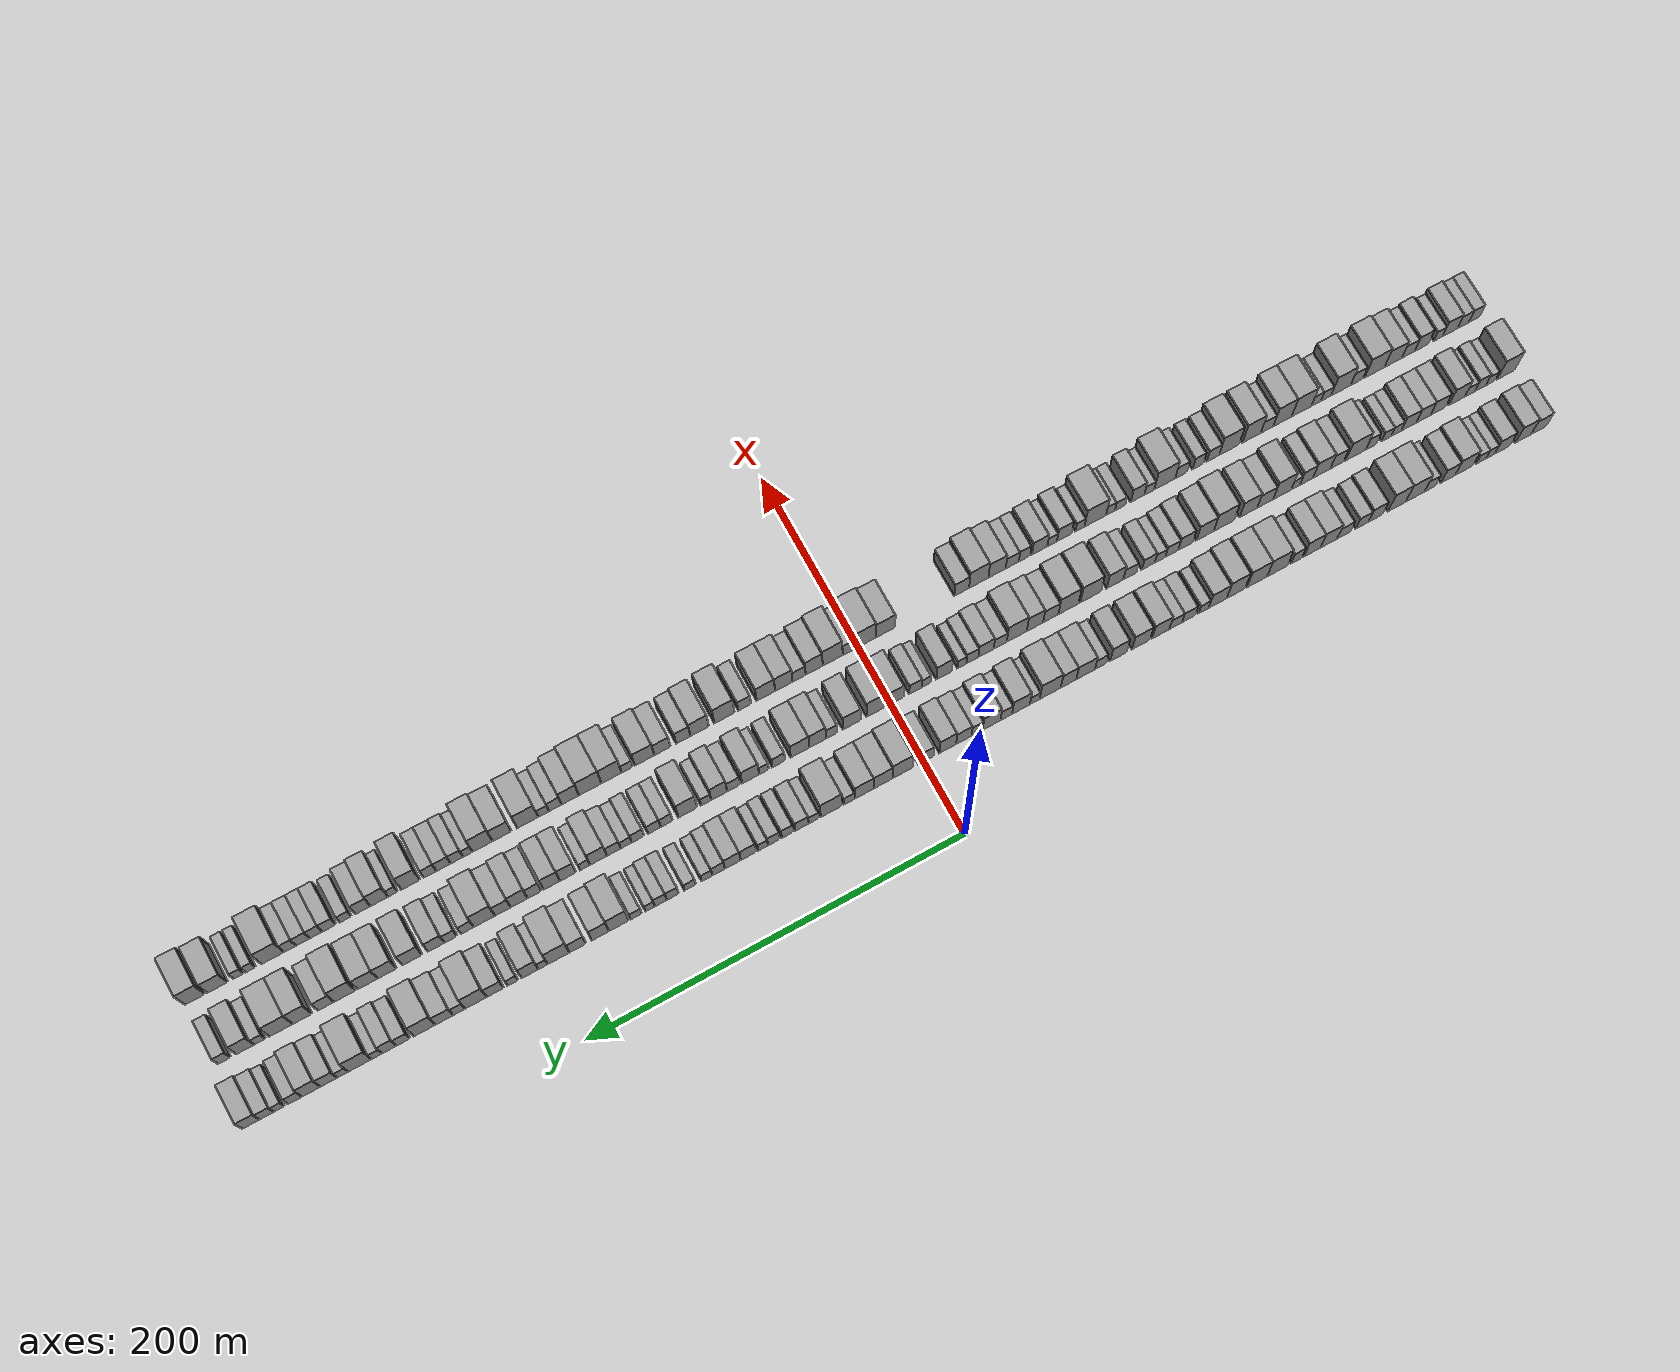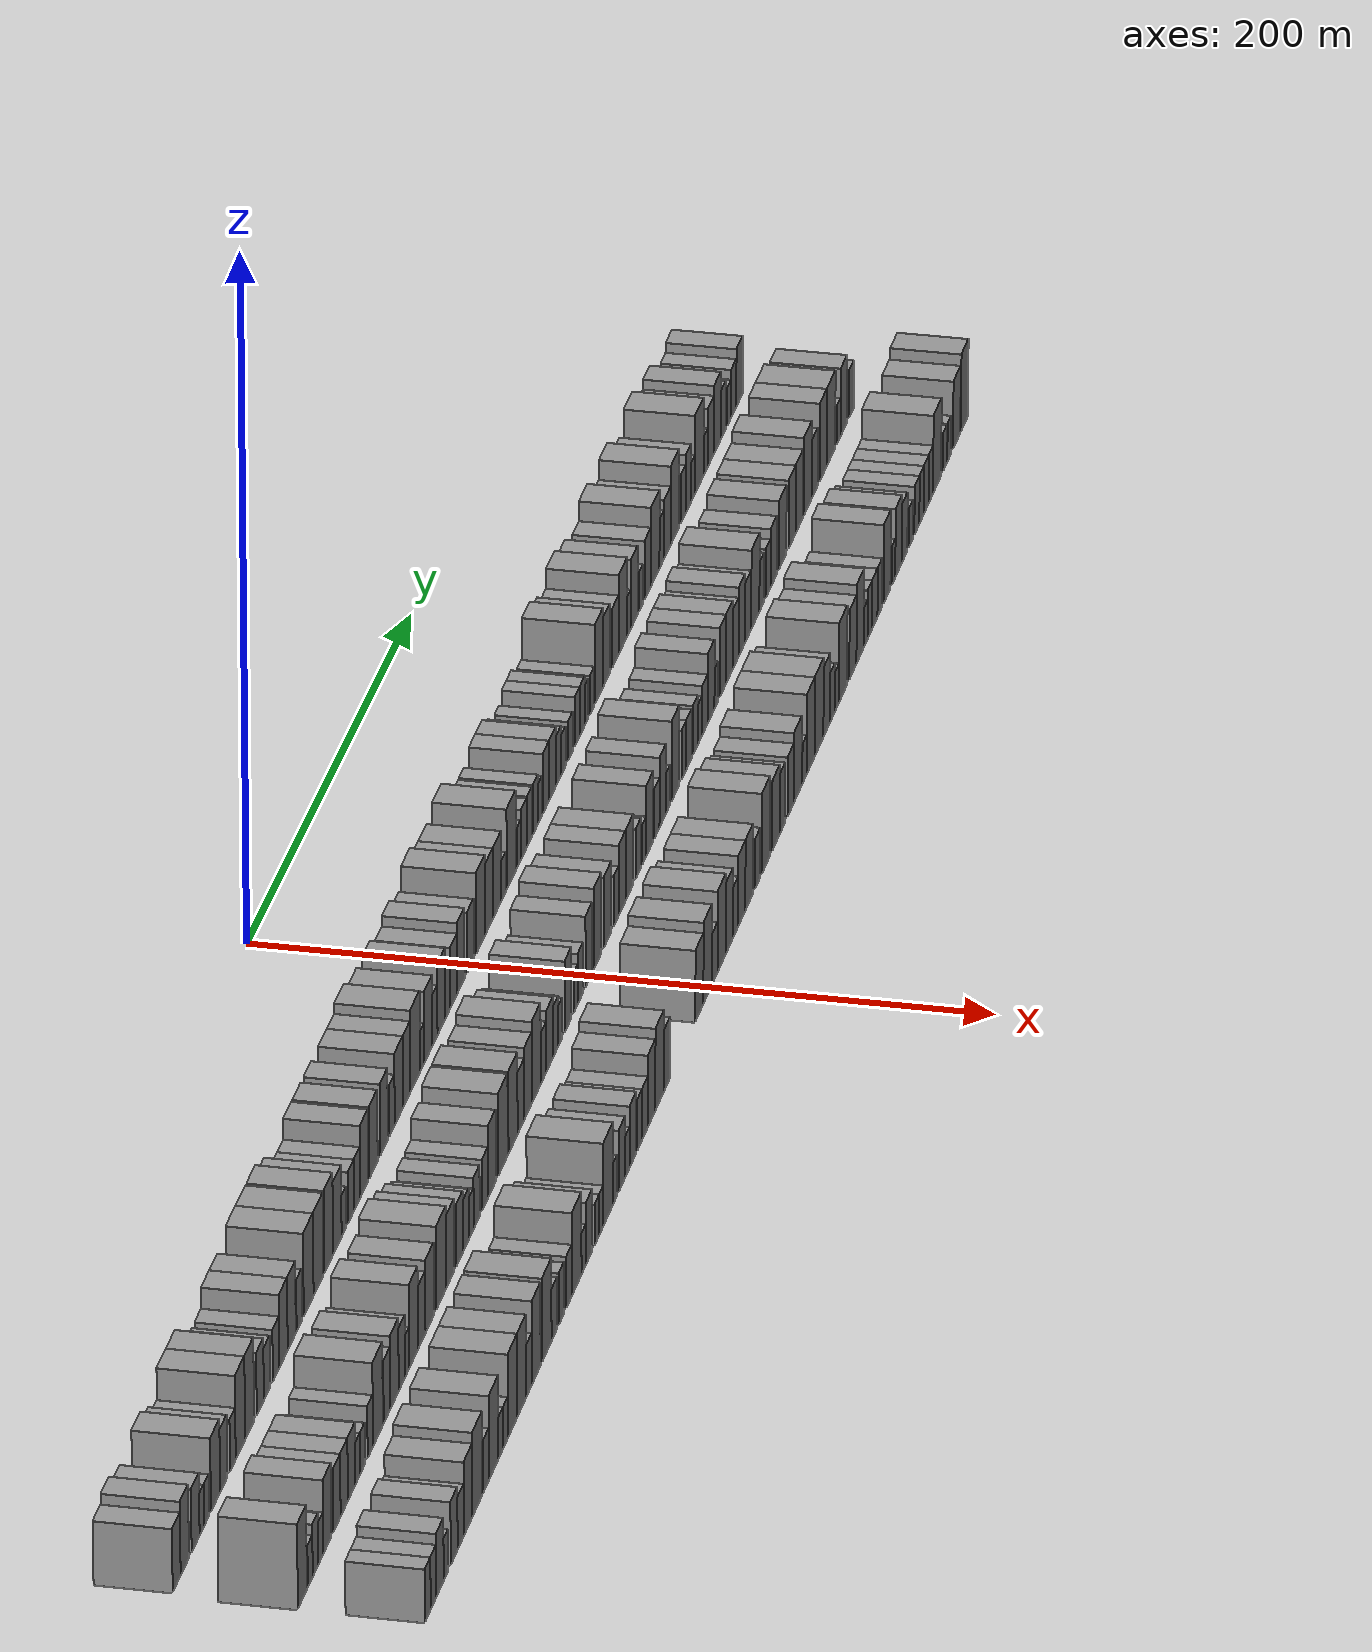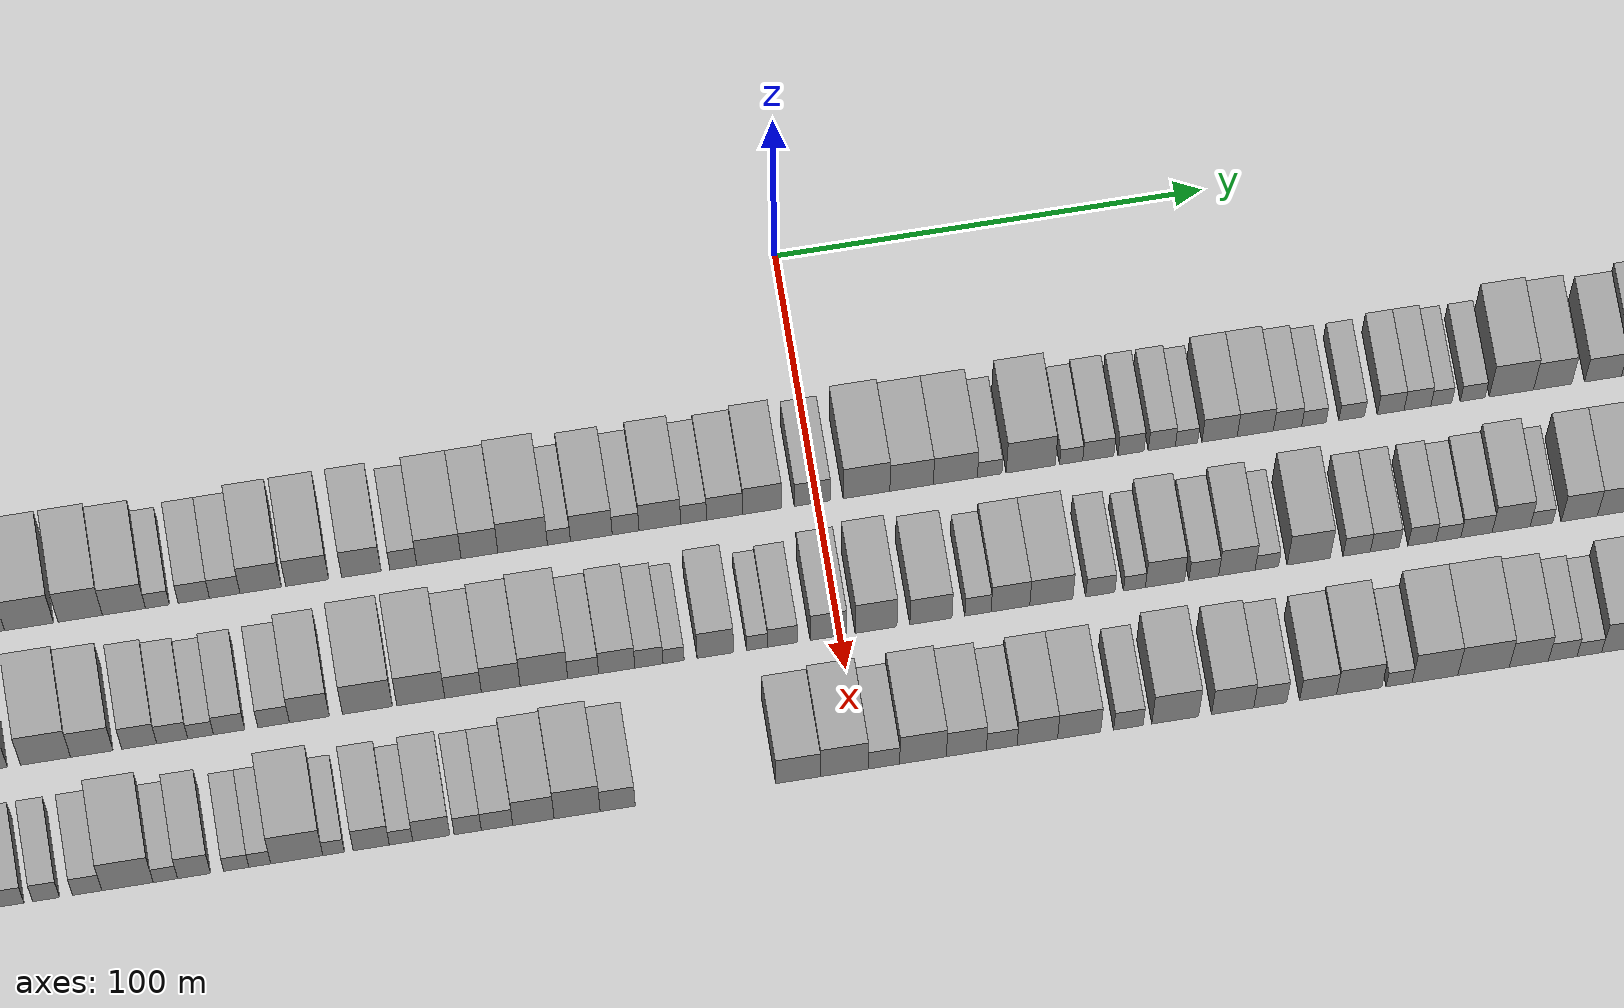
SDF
<sdf version="1.6">
 <world name="default">
  <scene>
   <sky><clouds><speed>12</speed></clouds></sky>
   <ambient>0.4 0.4 0.4 1</ambient>
   <background>0.7 0.7 0.7 1</background>
   <shadows>1</shadows>
  </scene>
  <gravity>0 0 -9.8066</gravity>
  <magnetic_field>6e-06 2.3e-05 -4.2e-05</magnetic_field>
  <physics default="0" name="default_physics" type="ode">
   <ode>
    <solver>
     <type>quick</type>
     <iters>10</iters>
     <sor>1.0</sor>
     <use_dynamic_moi_rescaling>0</use_dynamic_moi_rescaling>
    </solver>
    <constraints>
     <cfm>0</cfm>
     <erp>0.2</erp>
     <contact_max_correcting_vel>100</contact_max_correcting_vel>
     <contact_surface_layer>0.001</contact_surface_layer>
    </constraints>
   </ode>
   <max_step_size>0.004</max_step_size>
   <real_time_factor>1</real_time_factor>
   <real_time_update_rate>250</real_time_update_rate>
  </physics>
  <light name="sun" type="directional">
   <pose>0 0 10 0 0 0</pose>
   <diffuse>0.8 0.8 0.8 1</diffuse>
   <specular>0.2 0.2 0.2 1</specular>
   <attenuation>
    <range>1000</range>
    <constant>0.9</constant>
    <linear>0.01</linear>
    <quadratic>0.001</quadratic>
   </attenuation>
   <direction>-0.5 0.1 -0.9</direction>
  </light>
  <model name="building_1">
   <static>1</static>
   <pose>50.0000 -341.6680 0 0.000000 0.000000 0.000000</pose>
   <link name="link">
    <pose>0 0 9.00 0 0 0</pose>
    <collision name="collision"><geometry><box><size>20.0000 8.6639 18.0000</size></box></geometry></collision>
    <visual name="visual">
     <cast_shadows>0</cast_shadows>
     <geometry><box><size>20.0000 8.6639 18.0000</size></box></geometry>
     <material>
      <script>
       <uri>model://grey_wall/materials/scripts</uri>
       <uri>model://grey_wall/materials/textures</uri>
       <name>vrc/grey_wall</name>
      </script>
     </material>
    </visual>
   </link>
  </model>
  <model name="building_2">
   <static>1</static>
   <pose>50.0000 -332.8158 0 0.000000 0.000000 0.000000</pose>
   <link name="link">
    <pose>0 0 10.50 0 0 0</pose>
    <collision name="collision"><geometry><box><size>20.0000 9.0405 21.0000</size></box></geometry></collision>
    <visual name="visual">
     <cast_shadows>0</cast_shadows>
     <geometry><box><size>20.0000 9.0405 21.0000</size></box></geometry>
     <material>
      <script>
       <uri>model://grey_wall/materials/scripts</uri>
       <uri>model://grey_wall/materials/textures</uri>
       <name>vrc/grey_wall</name>
      </script>
     </material>
    </visual>
   </link>
  </model>
  <model name="building_3">
   <static>1</static>
   <pose>50.0000 -320.9205 0 0.000000 0.000000 0.000000</pose>
   <link name="link">
    <pose>0 0 9.00 0 0 0</pose>
    <collision name="collision"><geometry><box><size>20.0000 8.7500 18.0000</size></box></geometry></collision>
    <visual name="visual">
     <cast_shadows>0</cast_shadows>
     <geometry><box><size>20.0000 8.7500 18.0000</size></box></geometry>
     <material>
      <script>
       <uri>model://grey_wall/materials/scripts</uri>
       <uri>model://grey_wall/materials/textures</uri>
       <name>vrc/grey_wall</name>
      </script>
     </material>
    </visual>
   </link>
  </model>
  <model name="building_4">
   <static>1</static>
   <pose>50.0000 -314.0533 0 0.000000 0.000000 0.000000</pose>
   <link name="link">
    <pose>0 0 6.00 0 0 0</pose>
    <collision name="collision"><geometry><box><size>20.0000 4.9846 12.0000</size></box></geometry></collision>
    <visual name="visual">
     <cast_shadows>0</cast_shadows>
     <geometry><box><size>20.0000 4.9846 12.0000</size></box></geometry>
     <material>
      <script>
       <uri>model://grey_wall/materials/scripts</uri>
       <uri>model://grey_wall/materials/textures</uri>
       <name>vrc/grey_wall</name>
      </script>
     </material>
    </visual>
   </link>
  </model>
  <model name="building_5">
   <static>1</static>
   <pose>50.0000 -308.8026 0 0.000000 0.000000 0.000000</pose>
   <link name="link">
    <pose>0 0 6.00 0 0 0</pose>
    <collision name="collision"><geometry><box><size>20.0000 5.5168 12.0000</size></box></geometry></collision>
    <visual name="visual">
     <cast_shadows>0</cast_shadows>
     <geometry><box><size>20.0000 5.5168 12.0000</size></box></geometry>
     <material>
      <script>
       <uri>model://grey_wall/materials/scripts</uri>
       <uri>model://grey_wall/materials/textures</uri>
       <name>vrc/grey_wall</name>
      </script>
     </material>
    </visual>
   </link>
  </model>
  <model name="building_6">
   <static>1</static>
   <pose>50.0000 -298.9697 0 0.000000 0.000000 0.000000</pose>
   <link name="link">
    <pose>0 0 10.50 0 0 0</pose>
    <collision name="collision"><geometry><box><size>20.0000 10.1490 21.0000</size></box></geometry></collision>
    <visual name="visual">
     <cast_shadows>0</cast_shadows>
     <geometry><box><size>20.0000 10.1490 21.0000</size></box></geometry>
     <material>
      <script>
       <uri>model://grey_wall/materials/scripts</uri>
       <uri>model://grey_wall/materials/textures</uri>
       <name>vrc/grey_wall</name>
      </script>
     </material>
    </visual>
   </link>
  </model>
  <model name="building_7">
   <static>1</static>
   <pose>50.0000 -289.8867 0 0.000000 0.000000 0.000000</pose>
   <link name="link">
    <pose>0 0 9.00 0 0 0</pose>
    <collision name="collision"><geometry><box><size>20.0000 8.0170 18.0000</size></box></geometry></collision>
    <visual name="visual">
     <cast_shadows>0</cast_shadows>
     <geometry><box><size>20.0000 8.0170 18.0000</size></box></geometry>
     <material>
      <script>
       <uri>model://grey_wall/materials/scripts</uri>
       <uri>model://grey_wall/materials/textures</uri>
       <name>vrc/grey_wall</name>
      </script>
     </material>
    </visual>
   </link>
  </model>
  <model name="building_8">
   <static>1</static>
   <pose>50.0000 -279.6872 0 0.000000 0.000000 0.000000</pose>
   <link name="link">
    <pose>0 0 7.50 0 0 0</pose>
    <collision name="collision"><geometry><box><size>20.0000 6.3818 15.0000</size></box></geometry></collision>
    <visual name="visual">
     <cast_shadows>0</cast_shadows>
     <geometry><box><size>20.0000 6.3818 15.0000</size></box></geometry>
     <material>
      <script>
       <uri>model://grey_wall/materials/scripts</uri>
       <uri>model://grey_wall/materials/textures</uri>
       <name>vrc/grey_wall</name>
      </script>
     </material>
    </visual>
   </link>
  </model>
  <model name="building_9">
   <static>1</static>
   <pose>50.0000 -271.2123 0 0.000000 0.000000 0.000000</pose>
   <link name="link">
    <pose>0 0 12.00 0 0 0</pose>
    <collision name="collision"><geometry><box><size>20.0000 10.5679 24.0000</size></box></geometry></collision>
    <visual name="visual">
     <cast_shadows>0</cast_shadows>
     <geometry><box><size>20.0000 10.5679 24.0000</size></box></geometry>
     <material>
      <script>
       <uri>model://grey_wall/materials/scripts</uri>
       <uri>model://grey_wall/materials/textures</uri>
       <name>vrc/grey_wall</name>
      </script>
     </material>
    </visual>
   </link>
  </model>
  <model name="building_10">
   <static>1</static>
   <pose>50.0000 -260.9141 0 0.000000 0.000000 0.000000</pose>
   <link name="link">
    <pose>0 0 12.00 0 0 0</pose>
    <collision name="collision"><geometry><box><size>20.0000 10.0286 24.0000</size></box></geometry></collision>
    <visual name="visual">
     <cast_shadows>0</cast_shadows>
     <geometry><box><size>20.0000 10.0286 24.0000</size></box></geometry>
     <material>
      <script>
       <uri>model://grey_wall/materials/scripts</uri>
       <uri>model://grey_wall/materials/textures</uri>
       <name>vrc/grey_wall</name>
      </script>
     </material>
    </visual>
   </link>
  </model>
  <model name="building_11">
   <static>1</static>
   <pose>50.0000 -248.8983 0 0.000000 0.000000 0.000000</pose>
   <link name="link">
    <pose>0 0 9.00 0 0 0</pose>
    <collision name="collision"><geometry><box><size>20.0000 8.0029 18.0000</size></box></geometry></collision>
    <visual name="visual">
     <cast_shadows>0</cast_shadows>
     <geometry><box><size>20.0000 8.0029 18.0000</size></box></geometry>
     <material>
      <script>
       <uri>model://grey_wall/materials/scripts</uri>
       <uri>model://grey_wall/materials/textures</uri>
       <name>vrc/grey_wall</name>
      </script>
     </material>
    </visual>
   </link>
  </model>
  <model name="building_12">
   <static>1</static>
   <pose>50.0000 -241.3023 0 0.000000 0.000000 0.000000</pose>
   <link name="link">
    <pose>0 0 7.50 0 0 0</pose>
    <collision name="collision"><geometry><box><size>20.0000 7.1892 15.0000</size></box></geometry></collision>
    <visual name="visual">
     <cast_shadows>0</cast_shadows>
     <geometry><box><size>20.0000 7.1892 15.0000</size></box></geometry>
     <material>
      <script>
       <uri>model://grey_wall/materials/scripts</uri>
       <uri>model://grey_wall/materials/textures</uri>
       <name>vrc/grey_wall</name>
      </script>
     </material>
    </visual>
   </link>
  </model>
  <model name="building_13">
   <static>1</static>
   <pose>50.0000 -230.9784 0 0.000000 0.000000 0.000000</pose>
   <link name="link">
    <pose>0 0 7.50 0 0 0</pose>
    <collision name="collision"><geometry><box><size>20.0000 7.4584 15.0000</size></box></geometry></collision>
    <visual name="visual">
     <cast_shadows>0</cast_shadows>
     <geometry><box><size>20.0000 7.4584 15.0000</size></box></geometry>
     <material>
      <script>
       <uri>model://grey_wall/materials/scripts</uri>
       <uri>model://grey_wall/materials/textures</uri>
       <name>vrc/grey_wall</name>
      </script>
     </material>
    </visual>
   </link>
  </model>
  <model name="building_14">
   <static>1</static>
   <pose>50.0000 -222.5183 0 0.000000 0.000000 0.000000</pose>
   <link name="link">
    <pose>0 0 10.50 0 0 0</pose>
    <collision name="collision"><geometry><box><size>20.0000 9.4620 21.0000</size></box></geometry></collision>
    <visual name="visual">
     <cast_shadows>0</cast_shadows>
     <geometry><box><size>20.0000 9.4620 21.0000</size></box></geometry>
     <material>
      <script>
       <uri>model://grey_wall/materials/scripts</uri>
       <uri>model://grey_wall/materials/textures</uri>
       <name>vrc/grey_wall</name>
      </script>
     </material>
    </visual>
   </link>
  </model>
  <model name="building_15">
   <static>1</static>
   <pose>50.0000 -213.1940 0 0.000000 0.000000 0.000000</pose>
   <link name="link">
    <pose>0 0 10.50 0 0 0</pose>
    <collision name="collision"><geometry><box><size>20.0000 9.1866 21.0000</size></box></geometry></collision>
    <visual name="visual">
     <cast_shadows>0</cast_shadows>
     <geometry><box><size>20.0000 9.1866 21.0000</size></box></geometry>
     <material>
      <script>
       <uri>model://grey_wall/materials/scripts</uri>
       <uri>model://grey_wall/materials/textures</uri>
       <name>vrc/grey_wall</name>
      </script>
     </material>
    </visual>
   </link>
  </model>
  <model name="building_16">
   <static>1</static>
   <pose>50.0000 -204.5228 0 0.000000 0.000000 0.000000</pose>
   <link name="link">
    <pose>0 0 7.50 0 0 0</pose>
    <collision name="collision"><geometry><box><size>20.0000 6.1557 15.0000</size></box></geometry></collision>
    <visual name="visual">
     <cast_shadows>0</cast_shadows>
     <geometry><box><size>20.0000 6.1557 15.0000</size></box></geometry>
     <material>
      <script>
       <uri>model://grey_wall/materials/scripts</uri>
       <uri>model://grey_wall/materials/textures</uri>
       <name>vrc/grey_wall</name>
      </script>
     </material>
    </visual>
   </link>
  </model>
  <model name="building_17">
   <static>1</static>
   <pose>50.0000 -193.7689 0 0.000000 0.000000 0.000000</pose>
   <link name="link">
    <pose>0 0 12.00 0 0 0</pose>
    <collision name="collision"><geometry><box><size>20.0000 11.3522 24.0000</size></box></geometry></collision>
    <visual name="visual">
     <cast_shadows>0</cast_shadows>
     <geometry><box><size>20.0000 11.3522 24.0000</size></box></geometry>
     <material>
      <script>
       <uri>model://grey_wall/materials/scripts</uri>
       <uri>model://grey_wall/materials/textures</uri>
       <name>vrc/grey_wall</name>
      </script>
     </material>
    </visual>
   </link>
  </model>
  <model name="building_18">
   <static>1</static>
   <pose>50.0000 -182.4504 0 0.000000 0.000000 0.000000</pose>
   <link name="link">
    <pose>0 0 12.00 0 0 0</pose>
    <collision name="collision"><geometry><box><size>20.0000 11.2848 24.0000</size></box></geometry></collision>
    <visual name="visual">
     <cast_shadows>0</cast_shadows>
     <geometry><box><size>20.0000 11.2848 24.0000</size></box></geometry>
     <material>
      <script>
       <uri>model://grey_wall/materials/scripts</uri>
       <uri>model://grey_wall/materials/textures</uri>
       <name>vrc/grey_wall</name>
      </script>
     </material>
    </visual>
   </link>
  </model>
  <model name="building_19">
   <static>1</static>
   <pose>50.0000 -170.6931 0 0.000000 0.000000 0.000000</pose>
   <link name="link">
    <pose>0 0 12.00 0 0 0</pose>
    <collision name="collision"><geometry><box><size>20.0000 10.2297 24.0000</size></box></geometry></collision>
    <visual name="visual">
     <cast_shadows>0</cast_shadows>
     <geometry><box><size>20.0000 10.2297 24.0000</size></box></geometry>
     <material>
      <script>
       <uri>model://grey_wall/materials/scripts</uri>
       <uri>model://grey_wall/materials/textures</uri>
       <name>vrc/grey_wall</name>
      </script>
     </material>
    </visual>
   </link>
  </model>
  <model name="building_20">
   <static>1</static>
   <pose>50.0000 -160.5894 0 0.000000 0.000000 0.000000</pose>
   <link name="link">
    <pose>0 0 10.50 0 0 0</pose>
    <collision name="collision"><geometry><box><size>20.0000 9.9778 21.0000</size></box></geometry></collision>
    <visual name="visual">
     <cast_shadows>0</cast_shadows>
     <geometry><box><size>20.0000 9.9778 21.0000</size></box></geometry>
     <material>
      <script>
       <uri>model://grey_wall/materials/scripts</uri>
       <uri>model://grey_wall/materials/textures</uri>
       <name>vrc/grey_wall</name>
      </script>
     </material>
    </visual>
   </link>
  </model>
  <model name="building_21">
   <static>1</static>
   <pose>50.0000 -152.8348 0 0.000000 0.000000 0.000000</pose>
   <link name="link">
    <pose>0 0 6.00 0 0 0</pose>
    <collision name="collision"><geometry><box><size>20.0000 5.5313 12.0000</size></box></geometry></collision>
    <visual name="visual">
     <cast_shadows>0</cast_shadows>
     <geometry><box><size>20.0000 5.5313 12.0000</size></box></geometry>
     <material>
      <script>
       <uri>model://grey_wall/materials/scripts</uri>
       <uri>model://grey_wall/materials/textures</uri>
       <name>vrc/grey_wall</name>
      </script>
     </material>
    </visual>
   </link>
  </model>
  <model name="building_22">
   <static>1</static>
   <pose>50.0000 -144.4515 0 0.000000 0.000000 0.000000</pose>
   <link name="link">
    <pose>0 0 7.50 0 0 0</pose>
    <collision name="collision"><geometry><box><size>20.0000 7.2354 15.0000</size></box></geometry></collision>
    <visual name="visual">
     <cast_shadows>0</cast_shadows>
     <geometry><box><size>20.0000 7.2354 15.0000</size></box></geometry>
     <material>
      <script>
       <uri>model://grey_wall/materials/scripts</uri>
       <uri>model://grey_wall/materials/textures</uri>
       <name>vrc/grey_wall</name>
      </script>
     </material>
    </visual>
   </link>
  </model>
  <model name="building_23">
   <static>1</static>
   <pose>50.0000 -137.3063 0 0.000000 0.000000 0.000000</pose>
   <link name="link">
    <pose>0 0 7.50 0 0 0</pose>
    <collision name="collision"><geometry><box><size>20.0000 7.0550 15.0000</size></box></geometry></collision>
    <visual name="visual">
     <cast_shadows>0</cast_shadows>
     <geometry><box><size>20.0000 7.0550 15.0000</size></box></geometry>
     <material>
      <script>
       <uri>model://grey_wall/materials/scripts</uri>
       <uri>model://grey_wall/materials/textures</uri>
       <name>vrc/grey_wall</name>
      </script>
     </material>
    </visual>
   </link>
  </model>
  <model name="building_24">
   <static>1</static>
   <pose>50.0000 -128.9969 0 0.000000 0.000000 0.000000</pose>
   <link name="link">
    <pose>0 0 10.50 0 0 0</pose>
    <collision name="collision"><geometry><box><size>20.0000 9.5638 21.0000</size></box></geometry></collision>
    <visual name="visual">
     <cast_shadows>0</cast_shadows>
     <geometry><box><size>20.0000 9.5638 21.0000</size></box></geometry>
     <material>
      <script>
       <uri>model://grey_wall/materials/scripts</uri>
       <uri>model://grey_wall/materials/textures</uri>
       <name>vrc/grey_wall</name>
      </script>
     </material>
    </visual>
   </link>
  </model>
  <model name="building_25">
   <static>1</static>
   <pose>50.0000 -118.2344 0 0.000000 0.000000 0.000000</pose>
   <link name="link">
    <pose>0 0 10.50 0 0 0</pose>
    <collision name="collision"><geometry><box><size>20.0000 9.9613 21.0000</size></box></geometry></collision>
    <visual name="visual">
     <cast_shadows>0</cast_shadows>
     <geometry><box><size>20.0000 9.9613 21.0000</size></box></geometry>
     <material>
      <script>
       <uri>model://grey_wall/materials/scripts</uri>
       <uri>model://grey_wall/materials/textures</uri>
       <name>vrc/grey_wall</name>
      </script>
     </material>
    </visual>
   </link>
  </model>
  <model name="building_26">
   <static>1</static>
   <pose>50.0000 -105.6971 0 0.000000 0.000000 0.000000</pose>
   <link name="link">
    <pose>0 0 10.50 0 0 0</pose>
    <collision name="collision"><geometry><box><size>20.0000 9.1133 21.0000</size></box></geometry></collision>
    <visual name="visual">
     <cast_shadows>0</cast_shadows>
     <geometry><box><size>20.0000 9.1133 21.0000</size></box></geometry>
     <material>
      <script>
       <uri>model://grey_wall/materials/scripts</uri>
       <uri>model://grey_wall/materials/textures</uri>
       <name>vrc/grey_wall</name>
      </script>
     </material>
    </visual>
   </link>
  </model>
  <model name="building_27">
   <static>1</static>
   <pose>50.0000 -96.0269 0 0.000000 0.000000 0.000000</pose>
   <link name="link">
    <pose>0 0 7.50 0 0 0</pose>
    <collision name="collision"><geometry><box><size>20.0000 6.2271 15.0000</size></box></geometry></collision>
    <visual name="visual">
     <cast_shadows>0</cast_shadows>
     <geometry><box><size>20.0000 6.2271 15.0000</size></box></geometry>
     <material>
      <script>
       <uri>model://grey_wall/materials/scripts</uri>
       <uri>model://grey_wall/materials/textures</uri>
       <name>vrc/grey_wall</name>
      </script>
     </material>
    </visual>
   </link>
  </model>
  <model name="building_28">
   <static>1</static>
   <pose>50.0000 -87.7738 0 0.000000 0.000000 0.000000</pose>
   <link name="link">
    <pose>0 0 10.50 0 0 0</pose>
    <collision name="collision"><geometry><box><size>20.0000 10.2791 21.0000</size></box></geometry></collision>
    <visual name="visual">
     <cast_shadows>0</cast_shadows>
     <geometry><box><size>20.0000 10.2791 21.0000</size></box></geometry>
     <material>
      <script>
       <uri>model://grey_wall/materials/scripts</uri>
       <uri>model://grey_wall/materials/textures</uri>
       <name>vrc/grey_wall</name>
      </script>
     </material>
    </visual>
   </link>
  </model>
  <model name="building_29">
   <static>1</static>
   <pose>50.0000 -78.3721 0 0.000000 0.000000 0.000000</pose>
   <link name="link">
    <pose>0 0 10.50 0 0 0</pose>
    <collision name="collision"><geometry><box><size>20.0000 8.5244 21.0000</size></box></geometry></collision>
    <visual name="visual">
     <cast_shadows>0</cast_shadows>
     <geometry><box><size>20.0000 8.5244 21.0000</size></box></geometry>
     <material>
      <script>
       <uri>model://grey_wall/materials/scripts</uri>
       <uri>model://grey_wall/materials/textures</uri>
       <name>vrc/grey_wall</name>
      </script>
     </material>
    </visual>
   </link>
  </model>
  <model name="building_30">
   <static>1</static>
   <pose>50.0000 -68.3717 0 0.000000 0.000000 0.000000</pose>
   <link name="link">
    <pose>0 0 12.00 0 0 0</pose>
    <collision name="collision"><geometry><box><size>20.0000 11.4764 24.0000</size></box></geometry></collision>
    <visual name="visual">
     <cast_shadows>0</cast_shadows>
     <geometry><box><size>20.0000 11.4764 24.0000</size></box></geometry>
     <material>
      <script>
       <uri>model://grey_wall/materials/scripts</uri>
       <uri>model://grey_wall/materials/textures</uri>
       <name>vrc/grey_wall</name>
      </script>
     </material>
    </visual>
   </link>
  </model>
  <model name="building_31">
   <static>1</static>
   <pose>50.0000 -59.9732 0 0.000000 0.000000 0.000000</pose>
   <link name="link">
    <pose>0 0 6.00 0 0 0</pose>
    <collision name="collision"><geometry><box><size>20.0000 5.3206 12.0000</size></box></geometry></collision>
    <visual name="visual">
     <cast_shadows>0</cast_shadows>
     <geometry><box><size>20.0000 5.3206 12.0000</size></box></geometry>
     <material>
      <script>
       <uri>model://grey_wall/materials/scripts</uri>
       <uri>model://grey_wall/materials/textures</uri>
       <name>vrc/grey_wall</name>
      </script>
     </material>
    </visual>
   </link>
  </model>
  <model name="building_32">
   <static>1</static>
   <pose>50.0000 -52.4652 0 0.000000 0.000000 0.000000</pose>
   <link name="link">
    <pose>0 0 10.50 0 0 0</pose>
    <collision name="collision"><geometry><box><size>20.0000 9.6953 21.0000</size></box></geometry></collision>
    <visual name="visual">
     <cast_shadows>0</cast_shadows>
     <geometry><box><size>20.0000 9.6953 21.0000</size></box></geometry>
     <material>
      <script>
       <uri>model://grey_wall/materials/scripts</uri>
       <uri>model://grey_wall/materials/textures</uri>
       <name>vrc/grey_wall</name>
      </script>
     </material>
    </visual>
   </link>
  </model>
  <model name="building_33">
   <static>1</static>
   <pose>50.0000 -44.5065 0 0.000000 0.000000 0.000000</pose>
   <link name="link">
    <pose>0 0 7.50 0 0 0</pose>
    <collision name="collision"><geometry><box><size>20.0000 6.2222 15.0000</size></box></geometry></collision>
    <visual name="visual">
     <cast_shadows>0</cast_shadows>
     <geometry><box><size>20.0000 6.2222 15.0000</size></box></geometry>
     <material>
      <script>
       <uri>model://grey_wall/materials/scripts</uri>
       <uri>model://grey_wall/materials/textures</uri>
       <name>vrc/grey_wall</name>
      </script>
     </material>
    </visual>
   </link>
  </model>
  <model name="building_34">
   <static>1</static>
   <pose>50.0000 -36.5536 0 0.000000 0.000000 0.000000</pose>
   <link name="link">
    <pose>0 0 10.50 0 0 0</pose>
    <collision name="collision"><geometry><box><size>20.0000 9.6836 21.0000</size></box></geometry></collision>
    <visual name="visual">
     <cast_shadows>0</cast_shadows>
     <geometry><box><size>20.0000 9.6836 21.0000</size></box></geometry>
     <material>
      <script>
       <uri>model://grey_wall/materials/scripts</uri>
       <uri>model://grey_wall/materials/textures</uri>
       <name>vrc/grey_wall</name>
      </script>
     </material>
    </visual>
   </link>
  </model>
  <model name="building_35">
   <static>1</static>
   <pose>50.0000 -28.7101 0 0.000000 0.000000 0.000000</pose>
   <link name="link">
    <pose>0 0 7.50 0 0 0</pose>
    <collision name="collision"><geometry><box><size>20.0000 6.0032 15.0000</size></box></geometry></collision>
    <visual name="visual">
     <cast_shadows>0</cast_shadows>
     <geometry><box><size>20.0000 6.0032 15.0000</size></box></geometry>
     <material>
      <script>
       <uri>model://grey_wall/materials/scripts</uri>
       <uri>model://grey_wall/materials/textures</uri>
       <name>vrc/grey_wall</name>
      </script>
     </material>
    </visual>
   </link>
  </model>
  <model name="building_36">
   <static>1</static>
   <pose>50.0000 -21.5175 0 0.000000 0.000000 0.000000</pose>
   <link name="link">
    <pose>0 0 9.00 0 0 0</pose>
    <collision name="collision"><geometry><box><size>20.0000 8.3821 18.0000</size></box></geometry></collision>
    <visual name="visual">
     <cast_shadows>0</cast_shadows>
     <geometry><box><size>20.0000 8.3821 18.0000</size></box></geometry>
     <material>
      <script>
       <uri>model://grey_wall/materials/scripts</uri>
       <uri>model://grey_wall/materials/textures</uri>
       <name>vrc/grey_wall</name>
      </script>
     </material>
    </visual>
   </link>
  </model>
  <model name="building_37">
   <static>1</static>
   <pose>50.0000 -12.8347 0 0.000000 0.000000 0.000000</pose>
   <link name="link">
    <pose>0 0 10.50 0 0 0</pose>
    <collision name="collision"><geometry><box><size>20.0000 8.9836 21.0000</size></box></geometry></collision>
    <visual name="visual">
     <cast_shadows>0</cast_shadows>
     <geometry><box><size>20.0000 8.9836 21.0000</size></box></geometry>
     <material>
      <script>
       <uri>model://grey_wall/materials/scripts</uri>
       <uri>model://grey_wall/materials/textures</uri>
       <name>vrc/grey_wall</name>
      </script>
     </material>
    </visual>
   </link>
  </model>
  <model name="building_38">
   <static>1</static>
   <pose>50.0000 -1.1734 0 0.000000 0.000000 0.000000</pose>
   <link name="link">
    <pose>0 0 9.00 0 0 0</pose>
    <collision name="collision"><geometry><box><size>20.0000 8.3390 18.0000</size></box></geometry></collision>
    <visual name="visual">
     <cast_shadows>0</cast_shadows>
     <geometry><box><size>20.0000 8.3390 18.0000</size></box></geometry>
     <material>
      <script>
       <uri>model://grey_wall/materials/scripts</uri>
       <uri>model://grey_wall/materials/textures</uri>
       <name>vrc/grey_wall</name>
      </script>
     </material>
    </visual>
   </link>
  </model>
  <model name="building_39">
   <static>1</static>
   <pose>50.0000 11.4217 0 0.000000 0.000000 0.000000</pose>
   <link name="link">
    <pose>0 0 12.00 0 0 0</pose>
    <collision name="collision"><geometry><box><size>20.0000 10.8511 24.0000</size></box></geometry></collision>
    <visual name="visual">
     <cast_shadows>0</cast_shadows>
     <geometry><box><size>20.0000 10.8511 24.0000</size></box></geometry>
     <material>
      <script>
       <uri>model://grey_wall/materials/scripts</uri>
       <uri>model://grey_wall/materials/textures</uri>
       <name>vrc/grey_wall</name>
      </script>
     </material>
    </visual>
   </link>
  </model>
  <model name="building_40">
   <static>1</static>
   <pose>50.0000 21.9112 0 0.000000 0.000000 0.000000</pose>
   <link name="link">
    <pose>0 0 10.50 0 0 0</pose>
    <collision name="collision"><geometry><box><size>20.0000 10.1278 21.0000</size></box></geometry></collision>
    <visual name="visual">
     <cast_shadows>0</cast_shadows>
     <geometry><box><size>20.0000 10.1278 21.0000</size></box></geometry>
     <material>
      <script>
       <uri>model://grey_wall/materials/scripts</uri>
       <uri>model://grey_wall/materials/textures</uri>
       <name>vrc/grey_wall</name>
      </script>
     </material>
    </visual>
   </link>
  </model>
  <model name="building_41">
   <static>1</static>
   <pose>50.0000 32.0943 0 0.000000 0.000000 0.000000</pose>
   <link name="link">
    <pose>0 0 10.50 0 0 0</pose>
    <collision name="collision"><geometry><box><size>20.0000 10.2385 21.0000</size></box></geometry></collision>
    <visual name="visual">
     <cast_shadows>0</cast_shadows>
     <geometry><box><size>20.0000 10.2385 21.0000</size></box></geometry>
     <material>
      <script>
       <uri>model://grey_wall/materials/scripts</uri>
       <uri>model://grey_wall/materials/textures</uri>
       <name>vrc/grey_wall</name>
      </script>
     </material>
    </visual>
   </link>
  </model>
  <model name="building_42">
   <static>1</static>
   <pose>50.0000 40.0651 0 0.000000 0.000000 0.000000</pose>
   <link name="link">
    <pose>0 0 6.00 0 0 0</pose>
    <collision name="collision"><geometry><box><size>20.0000 5.7032 12.0000</size></box></geometry></collision>
    <visual name="visual">
     <cast_shadows>0</cast_shadows>
     <geometry><box><size>20.0000 5.7032 12.0000</size></box></geometry>
     <material>
      <script>
       <uri>model://grey_wall/materials/scripts</uri>
       <uri>model://grey_wall/materials/textures</uri>
       <name>vrc/grey_wall</name>
      </script>
     </material>
    </visual>
   </link>
  </model>
  <model name="building_43">
   <static>1</static>
   <pose>50.0000 49.6296 0 0.000000 0.000000 0.000000</pose>
   <link name="link">
    <pose>0 0 12.00 0 0 0</pose>
    <collision name="collision"><geometry><box><size>20.0000 11.4258 24.0000</size></box></geometry></collision>
    <visual name="visual">
     <cast_shadows>0</cast_shadows>
     <geometry><box><size>20.0000 11.4258 24.0000</size></box></geometry>
     <material>
      <script>
       <uri>model://grey_wall/materials/scripts</uri>
       <uri>model://grey_wall/materials/textures</uri>
       <name>vrc/grey_wall</name>
      </script>
     </material>
    </visual>
   </link>
  </model>
  <model name="building_44">
   <static>1</static>
   <pose>50.0000 59.0430 0 0.000000 0.000000 0.000000</pose>
   <link name="link">
    <pose>0 0 6.00 0 0 0</pose>
    <collision name="collision"><geometry><box><size>20.0000 5.4010 12.0000</size></box></geometry></collision>
    <visual name="visual">
     <cast_shadows>0</cast_shadows>
     <geometry><box><size>20.0000 5.4010 12.0000</size></box></geometry>
     <material>
      <script>
       <uri>model://grey_wall/materials/scripts</uri>
       <uri>model://grey_wall/materials/textures</uri>
       <name>vrc/grey_wall</name>
      </script>
     </material>
    </visual>
   </link>
  </model>
  <model name="building_45">
   <static>1</static>
   <pose>50.0000 65.3539 0 0.000000 0.000000 0.000000</pose>
   <link name="link">
    <pose>0 0 7.50 0 0 0</pose>
    <collision name="collision"><geometry><box><size>20.0000 7.2207 15.0000</size></box></geometry></collision>
    <visual name="visual">
     <cast_shadows>0</cast_shadows>
     <geometry><box><size>20.0000 7.2207 15.0000</size></box></geometry>
     <material>
      <script>
       <uri>model://grey_wall/materials/scripts</uri>
       <uri>model://grey_wall/materials/textures</uri>
       <name>vrc/grey_wall</name>
      </script>
     </material>
    </visual>
   </link>
  </model>
  <model name="building_46">
   <static>1</static>
   <pose>50.0000 72.9925 0 0.000000 0.000000 0.000000</pose>
   <link name="link">
    <pose>0 0 7.50 0 0 0</pose>
    <collision name="collision"><geometry><box><size>20.0000 6.0565 15.0000</size></box></geometry></collision>
    <visual name="visual">
     <cast_shadows>0</cast_shadows>
     <geometry><box><size>20.0000 6.0565 15.0000</size></box></geometry>
     <material>
      <script>
       <uri>model://grey_wall/materials/scripts</uri>
       <uri>model://grey_wall/materials/textures</uri>
       <name>vrc/grey_wall</name>
      </script>
     </material>
    </visual>
   </link>
  </model>
  <model name="building_47">
   <static>1</static>
   <pose>50.0000 80.1737 0 0.000000 0.000000 0.000000</pose>
   <link name="link">
    <pose>0 0 7.50 0 0 0</pose>
    <collision name="collision"><geometry><box><size>20.0000 6.3059 15.0000</size></box></geometry></collision>
    <visual name="visual">
     <cast_shadows>0</cast_shadows>
     <geometry><box><size>20.0000 6.3059 15.0000</size></box></geometry>
     <material>
      <script>
       <uri>model://grey_wall/materials/scripts</uri>
       <uri>model://grey_wall/materials/textures</uri>
       <name>vrc/grey_wall</name>
      </script>
     </material>
    </visual>
   </link>
  </model>
  <model name="building_48">
   <static>1</static>
   <pose>50.0000 85.9237 0 0.000000 0.000000 0.000000</pose>
   <link name="link">
    <pose>0 0 6.00 0 0 0</pose>
    <collision name="collision"><geometry><box><size>20.0000 5.1941 12.0000</size></box></geometry></collision>
    <visual name="visual">
     <cast_shadows>0</cast_shadows>
     <geometry><box><size>20.0000 5.1941 12.0000</size></box></geometry>
     <material>
      <script>
       <uri>model://grey_wall/materials/scripts</uri>
       <uri>model://grey_wall/materials/textures</uri>
       <name>vrc/grey_wall</name>
      </script>
     </material>
    </visual>
   </link>
  </model>
  <model name="building_49">
   <static>1</static>
   <pose>50.0000 93.6527 0 0.000000 0.000000 0.000000</pose>
   <link name="link">
    <pose>0 0 9.00 0 0 0</pose>
    <collision name="collision"><geometry><box><size>20.0000 8.2641 18.0000</size></box></geometry></collision>
    <visual name="visual">
     <cast_shadows>0</cast_shadows>
     <geometry><box><size>20.0000 8.2641 18.0000</size></box></geometry>
     <material>
      <script>
       <uri>model://grey_wall/materials/scripts</uri>
       <uri>model://grey_wall/materials/textures</uri>
       <name>vrc/grey_wall</name>
      </script>
     </material>
    </visual>
   </link>
  </model>
  <model name="building_50">
   <static>1</static>
   <pose>50.0000 101.9920 0 0.000000 0.000000 0.000000</pose>
   <link name="link">
    <pose>0 0 9.00 0 0 0</pose>
    <collision name="collision"><geometry><box><size>20.0000 8.4146 18.0000</size></box></geometry></collision>
    <visual name="visual">
     <cast_shadows>0</cast_shadows>
     <geometry><box><size>20.0000 8.4146 18.0000</size></box></geometry>
     <material>
      <script>
       <uri>model://grey_wall/materials/scripts</uri>
       <uri>model://grey_wall/materials/textures</uri>
       <name>vrc/grey_wall</name>
      </script>
     </material>
    </visual>
   </link>
  </model>
  <model name="building_51">
   <static>1</static>
   <pose>50.0000 109.5094 0 0.000000 0.000000 0.000000</pose>
   <link name="link">
    <pose>0 0 7.50 0 0 0</pose>
    <collision name="collision"><geometry><box><size>20.0000 6.6202 15.0000</size></box></geometry></collision>
    <visual name="visual">
     <cast_shadows>0</cast_shadows>
     <geometry><box><size>20.0000 6.6202 15.0000</size></box></geometry>
     <material>
      <script>
       <uri>model://grey_wall/materials/scripts</uri>
       <uri>model://grey_wall/materials/textures</uri>
       <name>vrc/grey_wall</name>
      </script>
     </material>
    </visual>
   </link>
  </model>
  <model name="building_52">
   <static>1</static>
   <pose>50.0000 115.6537 0 0.000000 0.000000 0.000000</pose>
   <link name="link">
    <pose>0 0 6.00 0 0 0</pose>
    <collision name="collision"><geometry><box><size>20.0000 5.6683 12.0000</size></box></geometry></collision>
    <visual name="visual">
     <cast_shadows>0</cast_shadows>
     <geometry><box><size>20.0000 5.6683 12.0000</size></box></geometry>
     <material>
      <script>
       <uri>model://grey_wall/materials/scripts</uri>
       <uri>model://grey_wall/materials/textures</uri>
       <name>vrc/grey_wall</name>
      </script>
     </material>
    </visual>
   </link>
  </model>
  <model name="building_53">
   <static>1</static>
   <pose>50.0000 124.4864 0 0.000000 0.000000 0.000000</pose>
   <link name="link">
    <pose>0 0 6.00 0 0 0</pose>
    <collision name="collision"><geometry><box><size>20.0000 5.9971 12.0000</size></box></geometry></collision>
    <visual name="visual">
     <cast_shadows>0</cast_shadows>
     <geometry><box><size>20.0000 5.9971 12.0000</size></box></geometry>
     <material>
      <script>
       <uri>model://grey_wall/materials/scripts</uri>
       <uri>model://grey_wall/materials/textures</uri>
       <name>vrc/grey_wall</name>
      </script>
     </material>
    </visual>
   </link>
  </model>
  <model name="building_54">
   <static>1</static>
   <pose>50.0000 133.6102 0 0.000000 0.000000 0.000000</pose>
   <link name="link">
    <pose>0 0 7.50 0 0 0</pose>
    <collision name="collision"><geometry><box><size>20.0000 6.2505 15.0000</size></box></geometry></collision>
    <visual name="visual">
     <cast_shadows>0</cast_shadows>
     <geometry><box><size>20.0000 6.2505 15.0000</size></box></geometry>
     <material>
      <script>
       <uri>model://grey_wall/materials/scripts</uri>
       <uri>model://grey_wall/materials/textures</uri>
       <name>vrc/grey_wall</name>
      </script>
     </material>
    </visual>
   </link>
  </model>
  <model name="building_55">
   <static>1</static>
   <pose>50.0000 139.8593 0 0.000000 0.000000 0.000000</pose>
   <link name="link">
    <pose>0 0 7.50 0 0 0</pose>
    <collision name="collision"><geometry><box><size>20.0000 6.2476 15.0000</size></box></geometry></collision>
    <visual name="visual">
     <cast_shadows>0</cast_shadows>
     <geometry><box><size>20.0000 6.2476 15.0000</size></box></geometry>
     <material>
      <script>
       <uri>model://grey_wall/materials/scripts</uri>
       <uri>model://grey_wall/materials/textures</uri>
       <name>vrc/grey_wall</name>
      </script>
     </material>
    </visual>
   </link>
  </model>
  <model name="building_56">
   <static>1</static>
   <pose>50.0000 145.4303 0 0.000000 0.000000 0.000000</pose>
   <link name="link">
    <pose>0 0 6.00 0 0 0</pose>
    <collision name="collision"><geometry><box><size>20.0000 4.8945 12.0000</size></box></geometry></collision>
    <visual name="visual">
     <cast_shadows>0</cast_shadows>
     <geometry><box><size>20.0000 4.8945 12.0000</size></box></geometry>
     <material>
      <script>
       <uri>model://grey_wall/materials/scripts</uri>
       <uri>model://grey_wall/materials/textures</uri>
       <name>vrc/grey_wall</name>
      </script>
     </material>
    </visual>
   </link>
  </model>
  <model name="building_57">
   <static>1</static>
   <pose>50.0000 152.7708 0 0.000000 0.000000 0.000000</pose>
   <link name="link">
    <pose>0 0 6.00 0 0 0</pose>
    <collision name="collision"><geometry><box><size>20.0000 5.7866 12.0000</size></box></geometry></collision>
    <visual name="visual">
     <cast_shadows>0</cast_shadows>
     <geometry><box><size>20.0000 5.7866 12.0000</size></box></geometry>
     <material>
      <script>
       <uri>model://grey_wall/materials/scripts</uri>
       <uri>model://grey_wall/materials/textures</uri>
       <name>vrc/grey_wall</name>
      </script>
     </material>
    </visual>
   </link>
  </model>
  <model name="building_58">
   <static>1</static>
   <pose>50.0000 161.8327 0 0.000000 0.000000 0.000000</pose>
   <link name="link">
    <pose>0 0 12.00 0 0 0</pose>
    <collision name="collision"><geometry><box><size>20.0000 10.3371 24.0000</size></box></geometry></collision>
    <visual name="visual">
     <cast_shadows>0</cast_shadows>
     <geometry><box><size>20.0000 10.3371 24.0000</size></box></geometry>
     <material>
      <script>
       <uri>model://grey_wall/materials/scripts</uri>
       <uri>model://grey_wall/materials/textures</uri>
       <name>vrc/grey_wall</name>
      </script>
     </material>
    </visual>
   </link>
  </model>
  <model name="building_59">
   <static>1</static>
   <pose>50.0000 171.4739 0 0.000000 0.000000 0.000000</pose>
   <link name="link">
    <pose>0 0 10.50 0 0 0</pose>
    <collision name="collision"><geometry><box><size>20.0000 8.9453 21.0000</size></box></geometry></collision>
    <visual name="visual">
     <cast_shadows>0</cast_shadows>
     <geometry><box><size>20.0000 8.9453 21.0000</size></box></geometry>
     <material>
      <script>
       <uri>model://grey_wall/materials/scripts</uri>
       <uri>model://grey_wall/materials/textures</uri>
       <name>vrc/grey_wall</name>
      </script>
     </material>
    </visual>
   </link>
  </model>
  <model name="building_60">
   <static>1</static>
   <pose>50.0000 183.2740 0 0.000000 0.000000 0.000000</pose>
   <link name="link">
    <pose>0 0 9.00 0 0 0</pose>
    <collision name="collision"><geometry><box><size>20.0000 8.6550 18.0000</size></box></geometry></collision>
    <visual name="visual">
     <cast_shadows>0</cast_shadows>
     <geometry><box><size>20.0000 8.6550 18.0000</size></box></geometry>
     <material>
      <script>
       <uri>model://grey_wall/materials/scripts</uri>
       <uri>model://grey_wall/materials/textures</uri>
       <name>vrc/grey_wall</name>
      </script>
     </material>
    </visual>
   </link>
  </model>
  <model name="building_61">
   <static>1</static>
   <pose>50.0000 193.2526 0 0.000000 0.000000 0.000000</pose>
   <link name="link">
    <pose>0 0 12.00 0 0 0</pose>
    <collision name="collision"><geometry><box><size>20.0000 11.3021 24.0000</size></box></geometry></collision>
    <visual name="visual">
     <cast_shadows>0</cast_shadows>
     <geometry><box><size>20.0000 11.3021 24.0000</size></box></geometry>
     <material>
      <script>
       <uri>model://grey_wall/materials/scripts</uri>
       <uri>model://grey_wall/materials/textures</uri>
       <name>vrc/grey_wall</name>
      </script>
     </material>
    </visual>
   </link>
  </model>
  <model name="building_62">
   <static>1</static>
   <pose>50.0000 201.3147 0 0.000000 0.000000 0.000000</pose>
   <link name="link">
    <pose>0 0 6.00 0 0 0</pose>
    <collision name="collision"><geometry><box><size>20.0000 4.8221 12.0000</size></box></geometry></collision>
    <visual name="visual">
     <cast_shadows>0</cast_shadows>
     <geometry><box><size>20.0000 4.8221 12.0000</size></box></geometry>
     <material>
      <script>
       <uri>model://grey_wall/materials/scripts</uri>
       <uri>model://grey_wall/materials/textures</uri>
       <name>vrc/grey_wall</name>
      </script>
     </material>
    </visual>
   </link>
  </model>
  <model name="building_63">
   <static>1</static>
   <pose>50.0000 208.0464 0 0.000000 0.000000 0.000000</pose>
   <link name="link">
    <pose>0 0 10.50 0 0 0</pose>
    <collision name="collision"><geometry><box><size>20.0000 8.6414 21.0000</size></box></geometry></collision>
    <visual name="visual">
     <cast_shadows>0</cast_shadows>
     <geometry><box><size>20.0000 8.6414 21.0000</size></box></geometry>
     <material>
      <script>
       <uri>model://grey_wall/materials/scripts</uri>
       <uri>model://grey_wall/materials/textures</uri>
       <name>vrc/grey_wall</name>
      </script>
     </material>
    </visual>
   </link>
  </model>
  <model name="building_64">
   <static>1</static>
   <pose>50.0000 217.0051 0 0.000000 0.000000 0.000000</pose>
   <link name="link">
    <pose>0 0 6.00 0 0 0</pose>
    <collision name="collision"><geometry><box><size>20.0000 5.2760 12.0000</size></box></geometry></collision>
    <visual name="visual">
     <cast_shadows>0</cast_shadows>
     <geometry><box><size>20.0000 5.2760 12.0000</size></box></geometry>
     <material>
      <script>
       <uri>model://grey_wall/materials/scripts</uri>
       <uri>model://grey_wall/materials/textures</uri>
       <name>vrc/grey_wall</name>
      </script>
     </material>
    </visual>
   </link>
  </model>
  <model name="building_65">
   <static>1</static>
   <pose>50.0000 226.0107 0 0.000000 0.000000 0.000000</pose>
   <link name="link">
    <pose>0 0 9.00 0 0 0</pose>
    <collision name="collision"><geometry><box><size>20.0000 8.7353 18.0000</size></box></geometry></collision>
    <visual name="visual">
     <cast_shadows>0</cast_shadows>
     <geometry><box><size>20.0000 8.7353 18.0000</size></box></geometry>
     <material>
      <script>
       <uri>model://grey_wall/materials/scripts</uri>
       <uri>model://grey_wall/materials/textures</uri>
       <name>vrc/grey_wall</name>
      </script>
     </material>
    </visual>
   </link>
  </model>
  <model name="building_66">
   <static>1</static>
   <pose>50.0000 235.9674 0 0.000000 0.000000 0.000000</pose>
   <link name="link">
    <pose>0 0 12.00 0 0 0</pose>
    <collision name="collision"><geometry><box><size>20.0000 11.1779 24.0000</size></box></geometry></collision>
    <visual name="visual">
     <cast_shadows>0</cast_shadows>
     <geometry><box><size>20.0000 11.1779 24.0000</size></box></geometry>
     <material>
      <script>
       <uri>model://grey_wall/materials/scripts</uri>
       <uri>model://grey_wall/materials/textures</uri>
       <name>vrc/grey_wall</name>
      </script>
     </material>
    </visual>
   </link>
  </model>
  <model name="building_67">
   <static>1</static>
   <pose>50.0000 244.6649 0 0.000000 0.000000 0.000000</pose>
   <link name="link">
    <pose>0 0 7.50 0 0 0</pose>
    <collision name="collision"><geometry><box><size>20.0000 6.2172 15.0000</size></box></geometry></collision>
    <visual name="visual">
     <cast_shadows>0</cast_shadows>
     <geometry><box><size>20.0000 6.2172 15.0000</size></box></geometry>
     <material>
      <script>
       <uri>model://grey_wall/materials/scripts</uri>
       <uri>model://grey_wall/materials/textures</uri>
       <name>vrc/grey_wall</name>
      </script>
     </material>
    </visual>
   </link>
  </model>
  <model name="building_68">
   <static>1</static>
   <pose>50.0000 252.2728 0 0.000000 0.000000 0.000000</pose>
   <link name="link">
    <pose>0 0 9.00 0 0 0</pose>
    <collision name="collision"><geometry><box><size>20.0000 8.9987 18.0000</size></box></geometry></collision>
    <visual name="visual">
     <cast_shadows>0</cast_shadows>
     <geometry><box><size>20.0000 8.9987 18.0000</size></box></geometry>
     <material>
      <script>
       <uri>model://grey_wall/materials/scripts</uri>
       <uri>model://grey_wall/materials/textures</uri>
       <name>vrc/grey_wall</name>
      </script>
     </material>
    </visual>
   </link>
  </model>
  <model name="building_69">
   <static>1</static>
   <pose>50.0000 262.3515 0 0.000000 0.000000 0.000000</pose>
   <link name="link">
    <pose>0 0 12.00 0 0 0</pose>
    <collision name="collision"><geometry><box><size>20.0000 11.1586 24.0000</size></box></geometry></collision>
    <visual name="visual">
     <cast_shadows>0</cast_shadows>
     <geometry><box><size>20.0000 11.1586 24.0000</size></box></geometry>
     <material>
      <script>
       <uri>model://grey_wall/materials/scripts</uri>
       <uri>model://grey_wall/materials/textures</uri>
       <name>vrc/grey_wall</name>
      </script>
     </material>
    </visual>
   </link>
  </model>
  <model name="building_70">
   <static>1</static>
   <pose>50.0000 273.4029 0 0.000000 0.000000 0.000000</pose>
   <link name="link">
    <pose>0 0 7.50 0 0 0</pose>
    <collision name="collision"><geometry><box><size>20.0000 6.9441 15.0000</size></box></geometry></collision>
    <visual name="visual">
     <cast_shadows>0</cast_shadows>
     <geometry><box><size>20.0000 6.9441 15.0000</size></box></geometry>
     <material>
      <script>
       <uri>model://grey_wall/materials/scripts</uri>
       <uri>model://grey_wall/materials/textures</uri>
       <name>vrc/grey_wall</name>
      </script>
     </material>
    </visual>
   </link>
  </model>
  <model name="building_71">
   <static>1</static>
   <pose>50.0000 280.5089 0 0.000000 0.000000 0.000000</pose>
   <link name="link">
    <pose>0 0 9.00 0 0 0</pose>
    <collision name="collision"><geometry><box><size>20.0000 7.2680 18.0000</size></box></geometry></collision>
    <visual name="visual">
     <cast_shadows>0</cast_shadows>
     <geometry><box><size>20.0000 7.2680 18.0000</size></box></geometry>
     <material>
      <script>
       <uri>model://grey_wall/materials/scripts</uri>
       <uri>model://grey_wall/materials/textures</uri>
       <name>vrc/grey_wall</name>
      </script>
     </material>
    </visual>
   </link>
  </model>
  <model name="building_72">
   <static>1</static>
   <pose>50.0000 286.8468 0 0.000000 0.000000 0.000000</pose>
   <link name="link">
    <pose>0 0 6.00 0 0 0</pose>
    <collision name="collision"><geometry><box><size>20.0000 5.4077 12.0000</size></box></geometry></collision>
    <visual name="visual">
     <cast_shadows>0</cast_shadows>
     <geometry><box><size>20.0000 5.4077 12.0000</size></box></geometry>
     <material>
      <script>
       <uri>model://grey_wall/materials/scripts</uri>
       <uri>model://grey_wall/materials/textures</uri>
       <name>vrc/grey_wall</name>
      </script>
     </material>
    </visual>
   </link>
  </model>
  <model name="building_73">
   <static>1</static>
   <pose>50.0000 295.4719 0 0.000000 0.000000 0.000000</pose>
   <link name="link">
    <pose>0 0 12.00 0 0 0</pose>
    <collision name="collision"><geometry><box><size>20.0000 11.8426 24.0000</size></box></geometry></collision>
    <visual name="visual">
     <cast_shadows>0</cast_shadows>
     <geometry><box><size>20.0000 11.8426 24.0000</size></box></geometry>
     <material>
      <script>
       <uri>model://grey_wall/materials/scripts</uri>
       <uri>model://grey_wall/materials/textures</uri>
       <name>vrc/grey_wall</name>
      </script>
     </material>
    </visual>
   </link>
  </model>
  <model name="building_74">
   <static>1</static>
   <pose>50.0000 304.2046 0 0.000000 0.000000 0.000000</pose>
   <link name="link">
    <pose>0 0 6.00 0 0 0</pose>
    <collision name="collision"><geometry><box><size>20.0000 5.6226 12.0000</size></box></geometry></collision>
    <visual name="visual">
     <cast_shadows>0</cast_shadows>
     <geometry><box><size>20.0000 5.6226 12.0000</size></box></geometry>
     <material>
      <script>
       <uri>model://grey_wall/materials/scripts</uri>
       <uri>model://grey_wall/materials/textures</uri>
       <name>vrc/grey_wall</name>
      </script>
     </material>
    </visual>
   </link>
  </model>
  <model name="building_75">
   <static>1</static>
   <pose>50.0000 311.2909 0 0.000000 0.000000 0.000000</pose>
   <link name="link">
    <pose>0 0 9.00 0 0 0</pose>
    <collision name="collision"><geometry><box><size>20.0000 8.5500 18.0000</size></box></geometry></collision>
    <visual name="visual">
     <cast_shadows>0</cast_shadows>
     <geometry><box><size>20.0000 8.5500 18.0000</size></box></geometry>
     <material>
      <script>
       <uri>model://grey_wall/materials/scripts</uri>
       <uri>model://grey_wall/materials/textures</uri>
       <name>vrc/grey_wall</name>
      </script>
     </material>
    </visual>
   </link>
  </model>
  <model name="building_76">
   <static>1</static>
   <pose>50.0000 320.2099 0 0.000000 0.000000 0.000000</pose>
   <link name="link">
    <pose>0 0 10.50 0 0 0</pose>
    <collision name="collision"><geometry><box><size>20.0000 9.2882 21.0000</size></box></geometry></collision>
    <visual name="visual">
     <cast_shadows>0</cast_shadows>
     <geometry><box><size>20.0000 9.2882 21.0000</size></box></geometry>
     <material>
      <script>
       <uri>model://grey_wall/materials/scripts</uri>
       <uri>model://grey_wall/materials/textures</uri>
       <name>vrc/grey_wall</name>
      </script>
     </material>
    </visual>
   </link>
  </model>
  <model name="building_77">
   <static>1</static>
   <pose>50.0000 328.3287 0 0.000000 0.000000 0.000000</pose>
   <link name="link">
    <pose>0 0 7.50 0 0 0</pose>
    <collision name="collision"><geometry><box><size>20.0000 6.9493 15.0000</size></box></geometry></collision>
    <visual name="visual">
     <cast_shadows>0</cast_shadows>
     <geometry><box><size>20.0000 6.9493 15.0000</size></box></geometry>
     <material>
      <script>
       <uri>model://grey_wall/materials/scripts</uri>
       <uri>model://grey_wall/materials/textures</uri>
       <name>vrc/grey_wall</name>
      </script>
     </material>
    </visual>
   </link>
  </model>
  <model name="building_78">
   <static>1</static>
   <pose>50.0000 336.4179 0 0.000000 0.000000 0.000000</pose>
   <link name="link">
    <pose>0 0 6.00 0 0 0</pose>
    <collision name="collision"><geometry><box><size>20.0000 5.2292 12.0000</size></box></geometry></collision>
    <visual name="visual">
     <cast_shadows>0</cast_shadows>
     <geometry><box><size>20.0000 5.2292 12.0000</size></box></geometry>
     <material>
      <script>
       <uri>model://grey_wall/materials/scripts</uri>
       <uri>model://grey_wall/materials/textures</uri>
       <name>vrc/grey_wall</name>
      </script>
     </material>
    </visual>
   </link>
  </model>
  <model name="building_79">
   <static>1</static>
   <pose>50.0000 342.6247 0 0.000000 0.000000 0.000000</pose>
   <link name="link">
    <pose>0 0 7.50 0 0 0</pose>
    <collision name="collision"><geometry><box><size>20.0000 7.1845 15.0000</size></box></geometry></collision>
    <visual name="visual">
     <cast_shadows>0</cast_shadows>
     <geometry><box><size>20.0000 7.1845 15.0000</size></box></geometry>
     <material>
      <script>
       <uri>model://grey_wall/materials/scripts</uri>
       <uri>model://grey_wall/materials/textures</uri>
       <name>vrc/grey_wall</name>
      </script>
     </material>
    </visual>
   </link>
  </model>
  <model name="building_80">
   <static>1</static>
   <pose>50.0000 350.6467 0 0.000000 0.000000 0.000000</pose>
   <link name="link">
    <pose>0 0 9.00 0 0 0</pose>
    <collision name="collision"><geometry><box><size>20.0000 8.8594 18.0000</size></box></geometry></collision>
    <visual name="visual">
     <cast_shadows>0</cast_shadows>
     <geometry><box><size>20.0000 8.8594 18.0000</size></box></geometry>
     <material>
      <script>
       <uri>model://grey_wall/materials/scripts</uri>
       <uri>model://grey_wall/materials/textures</uri>
       <name>vrc/grey_wall</name>
      </script>
     </material>
    </visual>
   </link>
  </model>
  <model name="building_81">
   <static>1</static>
   <pose>82.0000 -342.9613 0 0.000000 0.000000 0.000000</pose>
   <link name="link">
    <pose>0 0 12.00 0 0 0</pose>
    <collision name="collision"><geometry><box><size>20.0000 10.0775 24.0000</size></box></geometry></collision>
    <visual name="visual">
     <cast_shadows>0</cast_shadows>
     <geometry><box><size>20.0000 10.0775 24.0000</size></box></geometry>
     <material>
      <script>
       <uri>model://grey_wall/materials/scripts</uri>
       <uri>model://grey_wall/materials/textures</uri>
       <name>vrc/grey_wall</name>
      </script>
     </material>
    </visual>
   </link>
  </model>
  <model name="building_82">
   <static>1</static>
   <pose>82.0000 -334.1534 0 0.000000 0.000000 0.000000</pose>
   <link name="link">
    <pose>0 0 6.00 0 0 0</pose>
    <collision name="collision"><geometry><box><size>20.0000 5.5384 12.0000</size></box></geometry></collision>
    <visual name="visual">
     <cast_shadows>0</cast_shadows>
     <geometry><box><size>20.0000 5.5384 12.0000</size></box></geometry>
     <material>
      <script>
       <uri>model://grey_wall/materials/scripts</uri>
       <uri>model://grey_wall/materials/textures</uri>
       <name>vrc/grey_wall</name>
      </script>
     </material>
    </visual>
   </link>
  </model>
  <model name="building_83">
   <static>1</static>
   <pose>82.0000 -328.2987 0 0.000000 0.000000 0.000000</pose>
   <link name="link">
    <pose>0 0 7.50 0 0 0</pose>
    <collision name="collision"><geometry><box><size>20.0000 6.1709 15.0000</size></box></geometry></collision>
    <visual name="visual">
     <cast_shadows>0</cast_shadows>
     <geometry><box><size>20.0000 6.1709 15.0000</size></box></geometry>
     <material>
      <script>
       <uri>model://grey_wall/materials/scripts</uri>
       <uri>model://grey_wall/materials/textures</uri>
       <name>vrc/grey_wall</name>
      </script>
     </material>
    </visual>
   </link>
  </model>
  <model name="building_84">
   <static>1</static>
   <pose>82.0000 -322.3243 0 0.000000 0.000000 0.000000</pose>
   <link name="link">
    <pose>0 0 6.00 0 0 0</pose>
    <collision name="collision"><geometry><box><size>20.0000 5.7780 12.0000</size></box></geometry></collision>
    <visual name="visual">
     <cast_shadows>0</cast_shadows>
     <geometry><box><size>20.0000 5.7780 12.0000</size></box></geometry>
     <material>
      <script>
       <uri>model://grey_wall/materials/scripts</uri>
       <uri>model://grey_wall/materials/textures</uri>
       <name>vrc/grey_wall</name>
      </script>
     </material>
    </visual>
   </link>
  </model>
  <model name="building_85">
   <static>1</static>
   <pose>82.0000 -314.8796 0 0.000000 0.000000 0.000000</pose>
   <link name="link">
    <pose>0 0 10.50 0 0 0</pose>
    <collision name="collision"><geometry><box><size>20.0000 9.1114 21.0000</size></box></geometry></collision>
    <visual name="visual">
     <cast_shadows>0</cast_shadows>
     <geometry><box><size>20.0000 9.1114 21.0000</size></box></geometry>
     <material>
      <script>
       <uri>model://grey_wall/materials/scripts</uri>
       <uri>model://grey_wall/materials/textures</uri>
       <name>vrc/grey_wall</name>
      </script>
     </material>
    </visual>
   </link>
  </model>
  <model name="building_86">
   <static>1</static>
   <pose>82.0000 -304.0962 0 0.000000 0.000000 0.000000</pose>
   <link name="link">
    <pose>0 0 9.00 0 0 0</pose>
    <collision name="collision"><geometry><box><size>20.0000 8.4553 18.0000</size></box></geometry></collision>
    <visual name="visual">
     <cast_shadows>0</cast_shadows>
     <geometry><box><size>20.0000 8.4553 18.0000</size></box></geometry>
     <material>
      <script>
       <uri>model://grey_wall/materials/scripts</uri>
       <uri>model://grey_wall/materials/textures</uri>
       <name>vrc/grey_wall</name>
      </script>
     </material>
    </visual>
   </link>
  </model>
  <model name="building_87">
   <static>1</static>
   <pose>82.0000 -295.7610 0 0.000000 0.000000 0.000000</pose>
   <link name="link">
    <pose>0 0 9.00 0 0 0</pose>
    <collision name="collision"><geometry><box><size>20.0000 8.2152 18.0000</size></box></geometry></collision>
    <visual name="visual">
     <cast_shadows>0</cast_shadows>
     <geometry><box><size>20.0000 8.2152 18.0000</size></box></geometry>
     <material>
      <script>
       <uri>model://grey_wall/materials/scripts</uri>
       <uri>model://grey_wall/materials/textures</uri>
       <name>vrc/grey_wall</name>
      </script>
     </material>
    </visual>
   </link>
  </model>
  <model name="building_88">
   <static>1</static>
   <pose>82.0000 -287.3964 0 0.000000 0.000000 0.000000</pose>
   <link name="link">
    <pose>0 0 9.00 0 0 0</pose>
    <collision name="collision"><geometry><box><size>20.0000 8.5140 18.0000</size></box></geometry></collision>
    <visual name="visual">
     <cast_shadows>0</cast_shadows>
     <geometry><box><size>20.0000 8.5140 18.0000</size></box></geometry>
     <material>
      <script>
       <uri>model://grey_wall/materials/scripts</uri>
       <uri>model://grey_wall/materials/textures</uri>
       <name>vrc/grey_wall</name>
      </script>
     </material>
    </visual>
   </link>
  </model>
  <model name="building_89">
   <static>1</static>
   <pose>82.0000 -280.3068 0 0.000000 0.000000 0.000000</pose>
   <link name="link">
    <pose>0 0 6.00 0 0 0</pose>
    <collision name="collision"><geometry><box><size>20.0000 5.6651 12.0000</size></box></geometry></collision>
    <visual name="visual">
     <cast_shadows>0</cast_shadows>
     <geometry><box><size>20.0000 5.6651 12.0000</size></box></geometry>
     <material>
      <script>
       <uri>model://grey_wall/materials/scripts</uri>
       <uri>model://grey_wall/materials/textures</uri>
       <name>vrc/grey_wall</name>
      </script>
     </material>
    </visual>
   </link>
  </model>
  <model name="building_90">
   <static>1</static>
   <pose>82.0000 -274.7508 0 0.000000 0.000000 0.000000</pose>
   <link name="link">
    <pose>0 0 6.00 0 0 0</pose>
    <collision name="collision"><geometry><box><size>20.0000 5.4470 12.0000</size></box></geometry></collision>
    <visual name="visual">
     <cast_shadows>0</cast_shadows>
     <geometry><box><size>20.0000 5.4470 12.0000</size></box></geometry>
     <material>
      <script>
       <uri>model://grey_wall/materials/scripts</uri>
       <uri>model://grey_wall/materials/textures</uri>
       <name>vrc/grey_wall</name>
      </script>
     </material>
    </visual>
   </link>
  </model>
  <model name="building_91">
   <static>1</static>
   <pose>82.0000 -265.9827 0 0.000000 0.000000 0.000000</pose>
   <link name="link">
    <pose>0 0 7.50 0 0 0</pose>
    <collision name="collision"><geometry><box><size>20.0000 6.0891 15.0000</size></box></geometry></collision>
    <visual name="visual">
     <cast_shadows>0</cast_shadows>
     <geometry><box><size>20.0000 6.0891 15.0000</size></box></geometry>
     <material>
      <script>
       <uri>model://grey_wall/materials/scripts</uri>
       <uri>model://grey_wall/materials/textures</uri>
       <name>vrc/grey_wall</name>
      </script>
     </material>
    </visual>
   </link>
  </model>
  <model name="building_92">
   <static>1</static>
   <pose>82.0000 -257.2447 0 0.000000 0.000000 0.000000</pose>
   <link name="link">
    <pose>0 0 12.00 0 0 0</pose>
    <collision name="collision"><geometry><box><size>20.0000 11.3870 24.0000</size></box></geometry></collision>
    <visual name="visual">
     <cast_shadows>0</cast_shadows>
     <geometry><box><size>20.0000 11.3870 24.0000</size></box></geometry>
     <material>
      <script>
       <uri>model://grey_wall/materials/scripts</uri>
       <uri>model://grey_wall/materials/textures</uri>
       <name>vrc/grey_wall</name>
      </script>
     </material>
    </visual>
   </link>
  </model>
  <model name="building_93">
   <static>1</static>
   <pose>82.0000 -246.7193 0 0.000000 0.000000 0.000000</pose>
   <link name="link">
    <pose>0 0 9.00 0 0 0</pose>
    <collision name="collision"><geometry><box><size>20.0000 7.6638 18.0000</size></box></geometry></collision>
    <visual name="visual">
     <cast_shadows>0</cast_shadows>
     <geometry><box><size>20.0000 7.6638 18.0000</size></box></geometry>
     <material>
      <script>
       <uri>model://grey_wall/materials/scripts</uri>
       <uri>model://grey_wall/materials/textures</uri>
       <name>vrc/grey_wall</name>
      </script>
     </material>
    </visual>
   </link>
  </model>
  <model name="building_94">
   <static>1</static>
   <pose>82.0000 -237.9976 0 0.000000 0.000000 0.000000</pose>
   <link name="link">
    <pose>0 0 10.50 0 0 0</pose>
    <collision name="collision"><geometry><box><size>20.0000 9.7795 21.0000</size></box></geometry></collision>
    <visual name="visual">
     <cast_shadows>0</cast_shadows>
     <geometry><box><size>20.0000 9.7795 21.0000</size></box></geometry>
     <material>
      <script>
       <uri>model://grey_wall/materials/scripts</uri>
       <uri>model://grey_wall/materials/textures</uri>
       <name>vrc/grey_wall</name>
      </script>
     </material>
    </visual>
   </link>
  </model>
  <model name="building_95">
   <static>1</static>
   <pose>82.0000 -229.4237 0 0.000000 0.000000 0.000000</pose>
   <link name="link">
    <pose>0 0 9.00 0 0 0</pose>
    <collision name="collision"><geometry><box><size>20.0000 7.3684 18.0000</size></box></geometry></collision>
    <visual name="visual">
     <cast_shadows>0</cast_shadows>
     <geometry><box><size>20.0000 7.3684 18.0000</size></box></geometry>
     <material>
      <script>
       <uri>model://grey_wall/materials/scripts</uri>
       <uri>model://grey_wall/materials/textures</uri>
       <name>vrc/grey_wall</name>
      </script>
     </material>
    </visual>
   </link>
  </model>
  <model name="building_96">
   <static>1</static>
   <pose>82.0000 -223.2938 0 0.000000 0.000000 0.000000</pose>
   <link name="link">
    <pose>0 0 6.00 0 0 0</pose>
    <collision name="collision"><geometry><box><size>20.0000 4.8915 12.0000</size></box></geometry></collision>
    <visual name="visual">
     <cast_shadows>0</cast_shadows>
     <geometry><box><size>20.0000 4.8915 12.0000</size></box></geometry>
     <material>
      <script>
       <uri>model://grey_wall/materials/scripts</uri>
       <uri>model://grey_wall/materials/textures</uri>
       <name>vrc/grey_wall</name>
      </script>
     </material>
    </visual>
   </link>
  </model>
  <model name="building_97">
   <static>1</static>
   <pose>82.0000 -215.7499 0 0.000000 0.000000 0.000000</pose>
   <link name="link">
    <pose>0 0 12.00 0 0 0</pose>
    <collision name="collision"><geometry><box><size>20.0000 10.1962 24.0000</size></box></geometry></collision>
    <visual name="visual">
     <cast_shadows>0</cast_shadows>
     <geometry><box><size>20.0000 10.1962 24.0000</size></box></geometry>
     <material>
      <script>
       <uri>model://grey_wall/materials/scripts</uri>
       <uri>model://grey_wall/materials/textures</uri>
       <name>vrc/grey_wall</name>
      </script>
     </material>
    </visual>
   </link>
  </model>
  <model name="building_98">
   <static>1</static>
   <pose>82.0000 -206.2066 0 0.000000 0.000000 0.000000</pose>
   <link name="link">
    <pose>0 0 9.00 0 0 0</pose>
    <collision name="collision"><geometry><box><size>20.0000 8.8903 18.0000</size></box></geometry></collision>
    <visual name="visual">
     <cast_shadows>0</cast_shadows>
     <geometry><box><size>20.0000 8.8903 18.0000</size></box></geometry>
     <material>
      <script>
       <uri>model://grey_wall/materials/scripts</uri>
       <uri>model://grey_wall/materials/textures</uri>
       <name>vrc/grey_wall</name>
      </script>
     </material>
    </visual>
   </link>
  </model>
  <model name="building_99">
   <static>1</static>
   <pose>82.0000 -196.8253 0 0.000000 0.000000 0.000000</pose>
   <link name="link">
    <pose>0 0 10.50 0 0 0</pose>
    <collision name="collision"><geometry><box><size>20.0000 9.8723 21.0000</size></box></geometry></collision>
    <visual name="visual">
     <cast_shadows>0</cast_shadows>
     <geometry><box><size>20.0000 9.8723 21.0000</size></box></geometry>
     <material>
      <script>
       <uri>model://grey_wall/materials/scripts</uri>
       <uri>model://grey_wall/materials/textures</uri>
       <name>vrc/grey_wall</name>
      </script>
     </material>
    </visual>
   </link>
  </model>
  <model name="building_100">
   <static>1</static>
   <pose>82.0000 -183.1385 0 0.000000 0.000000 0.000000</pose>
   <link name="link">
    <pose>0 0 12.00 0 0 0</pose>
    <collision name="collision"><geometry><box><size>20.0000 11.5013 24.0000</size></box></geometry></collision>
    <visual name="visual">
     <cast_shadows>0</cast_shadows>
     <geometry><box><size>20.0000 11.5013 24.0000</size></box></geometry>
     <material>
      <script>
       <uri>model://grey_wall/materials/scripts</uri>
       <uri>model://grey_wall/materials/textures</uri>
       <name>vrc/grey_wall</name>
      </script>
     </material>
    </visual>
   </link>
  </model>
  <model name="building_101">
   <static>1</static>
   <pose>82.0000 -172.5107 0 0.000000 0.000000 0.000000</pose>
   <link name="link">
    <pose>0 0 10.50 0 0 0</pose>
    <collision name="collision"><geometry><box><size>20.0000 9.7541 21.0000</size></box></geometry></collision>
    <visual name="visual">
     <cast_shadows>0</cast_shadows>
     <geometry><box><size>20.0000 9.7541 21.0000</size></box></geometry>
     <material>
      <script>
       <uri>model://grey_wall/materials/scripts</uri>
       <uri>model://grey_wall/materials/textures</uri>
       <name>vrc/grey_wall</name>
      </script>
     </material>
    </visual>
   </link>
  </model>
  <model name="building_102">
   <static>1</static>
   <pose>82.0000 -161.6090 0 0.000000 0.000000 0.000000</pose>
   <link name="link">
    <pose>0 0 9.00 0 0 0</pose>
    <collision name="collision"><geometry><box><size>20.0000 8.0494 18.0000</size></box></geometry></collision>
    <visual name="visual">
     <cast_shadows>0</cast_shadows>
     <geometry><box><size>20.0000 8.0494 18.0000</size></box></geometry>
     <material>
      <script>
       <uri>model://grey_wall/materials/scripts</uri>
       <uri>model://grey_wall/materials/textures</uri>
       <name>vrc/grey_wall</name>
      </script>
     </material>
    </visual>
   </link>
  </model>
  <model name="building_103">
   <static>1</static>
   <pose>82.0000 -154.0170 0 0.000000 0.000000 0.000000</pose>
   <link name="link">
    <pose>0 0 7.50 0 0 0</pose>
    <collision name="collision"><geometry><box><size>20.0000 7.1347 15.0000</size></box></geometry></collision>
    <visual name="visual">
     <cast_shadows>0</cast_shadows>
     <geometry><box><size>20.0000 7.1347 15.0000</size></box></geometry>
     <material>
      <script>
       <uri>model://grey_wall/materials/scripts</uri>
       <uri>model://grey_wall/materials/textures</uri>
       <name>vrc/grey_wall</name>
      </script>
     </material>
    </visual>
   </link>
  </model>
  <model name="building_104">
   <static>1</static>
   <pose>82.0000 -147.4935 0 0.000000 0.000000 0.000000</pose>
   <link name="link">
    <pose>0 0 6.00 0 0 0</pose>
    <collision name="collision"><geometry><box><size>20.0000 5.9122 12.0000</size></box></geometry></collision>
    <visual name="visual">
     <cast_shadows>0</cast_shadows>
     <geometry><box><size>20.0000 5.9122 12.0000</size></box></geometry>
     <material>
      <script>
       <uri>model://grey_wall/materials/scripts</uri>
       <uri>model://grey_wall/materials/textures</uri>
       <name>vrc/grey_wall</name>
      </script>
     </material>
    </visual>
   </link>
  </model>
  <model name="building_105">
   <static>1</static>
   <pose>82.0000 -140.9353 0 0.000000 0.000000 0.000000</pose>
   <link name="link">
    <pose>0 0 7.50 0 0 0</pose>
    <collision name="collision"><geometry><box><size>20.0000 7.2043 15.0000</size></box></geometry></collision>
    <visual name="visual">
     <cast_shadows>0</cast_shadows>
     <geometry><box><size>20.0000 7.2043 15.0000</size></box></geometry>
     <material>
      <script>
       <uri>model://grey_wall/materials/scripts</uri>
       <uri>model://grey_wall/materials/textures</uri>
       <name>vrc/grey_wall</name>
      </script>
     </material>
    </visual>
   </link>
  </model>
  <model name="building_106">
   <static>1</static>
   <pose>82.0000 -130.6983 0 0.000000 0.000000 0.000000</pose>
   <link name="link">
    <pose>0 0 7.50 0 0 0</pose>
    <collision name="collision"><geometry><box><size>20.0000 7.2697 15.0000</size></box></geometry></collision>
    <visual name="visual">
     <cast_shadows>0</cast_shadows>
     <geometry><box><size>20.0000 7.2697 15.0000</size></box></geometry>
     <material>
      <script>
       <uri>model://grey_wall/materials/scripts</uri>
       <uri>model://grey_wall/materials/textures</uri>
       <name>vrc/grey_wall</name>
      </script>
     </material>
    </visual>
   </link>
  </model>
  <model name="building_107">
   <static>1</static>
   <pose>82.0000 -122.4626 0 0.000000 0.000000 0.000000</pose>
   <link name="link">
    <pose>0 0 10.50 0 0 0</pose>
    <collision name="collision"><geometry><box><size>20.0000 9.2019 21.0000</size></box></geometry></collision>
    <visual name="visual">
     <cast_shadows>0</cast_shadows>
     <geometry><box><size>20.0000 9.2019 21.0000</size></box></geometry>
     <material>
      <script>
       <uri>model://grey_wall/materials/scripts</uri>
       <uri>model://grey_wall/materials/textures</uri>
       <name>vrc/grey_wall</name>
      </script>
     </material>
    </visual>
   </link>
  </model>
  <model name="building_108">
   <static>1</static>
   <pose>82.0000 -109.0988 0 0.000000 0.000000 0.000000</pose>
   <link name="link">
    <pose>0 0 12.00 0 0 0</pose>
    <collision name="collision"><geometry><box><size>20.0000 11.5256 24.0000</size></box></geometry></collision>
    <visual name="visual">
     <cast_shadows>0</cast_shadows>
     <geometry><box><size>20.0000 11.5256 24.0000</size></box></geometry>
     <material>
      <script>
       <uri>model://grey_wall/materials/scripts</uri>
       <uri>model://grey_wall/materials/textures</uri>
       <name>vrc/grey_wall</name>
      </script>
     </material>
    </visual>
   </link>
  </model>
  <model name="building_109">
   <static>1</static>
   <pose>82.0000 -96.8106 0 0.000000 0.000000 0.000000</pose>
   <link name="link">
    <pose>0 0 12.00 0 0 0</pose>
    <collision name="collision"><geometry><box><size>20.0000 11.0509 24.0000</size></box></geometry></collision>
    <visual name="visual">
     <cast_shadows>0</cast_shadows>
     <geometry><box><size>20.0000 11.0509 24.0000</size></box></geometry>
     <material>
      <script>
       <uri>model://grey_wall/materials/scripts</uri>
       <uri>model://grey_wall/materials/textures</uri>
       <name>vrc/grey_wall</name>
      </script>
     </material>
    </visual>
   </link>
  </model>
  <model name="building_110">
   <static>1</static>
   <pose>82.0000 -87.0684 0 0.000000 0.000000 0.000000</pose>
   <link name="link">
    <pose>0 0 9.00 0 0 0</pose>
    <collision name="collision"><geometry><box><size>20.0000 8.4334 18.0000</size></box></geometry></collision>
    <visual name="visual">
     <cast_shadows>0</cast_shadows>
     <geometry><box><size>20.0000 8.4334 18.0000</size></box></geometry>
     <material>
      <script>
       <uri>model://grey_wall/materials/scripts</uri>
       <uri>model://grey_wall/materials/textures</uri>
       <name>vrc/grey_wall</name>
      </script>
     </material>
    </visual>
   </link>
  </model>
  <model name="building_111">
   <static>1</static>
   <pose>82.0000 -78.3703 0 0.000000 0.000000 0.000000</pose>
   <link name="link">
    <pose>0 0 10.50 0 0 0</pose>
    <collision name="collision"><geometry><box><size>20.0000 8.9630 21.0000</size></box></geometry></collision>
    <visual name="visual">
     <cast_shadows>0</cast_shadows>
     <geometry><box><size>20.0000 8.9630 21.0000</size></box></geometry>
     <material>
      <script>
       <uri>model://grey_wall/materials/scripts</uri>
       <uri>model://grey_wall/materials/textures</uri>
       <name>vrc/grey_wall</name>
      </script>
     </material>
    </visual>
   </link>
  </model>
  <model name="building_112">
   <static>1</static>
   <pose>82.0000 -68.4092 0 0.000000 0.000000 0.000000</pose>
   <link name="link">
    <pose>0 0 12.00 0 0 0</pose>
    <collision name="collision"><geometry><box><size>20.0000 10.9592 24.0000</size></box></geometry></collision>
    <visual name="visual">
     <cast_shadows>0</cast_shadows>
     <geometry><box><size>20.0000 10.9592 24.0000</size></box></geometry>
     <material>
      <script>
       <uri>model://grey_wall/materials/scripts</uri>
       <uri>model://grey_wall/materials/textures</uri>
       <name>vrc/grey_wall</name>
      </script>
     </material>
    </visual>
   </link>
  </model>
  <model name="building_113">
   <static>1</static>
   <pose>82.0000 -59.3602 0 0.000000 0.000000 0.000000</pose>
   <link name="link">
    <pose>0 0 7.50 0 0 0</pose>
    <collision name="collision"><geometry><box><size>20.0000 7.1387 15.0000</size></box></geometry></collision>
    <visual name="visual">
     <cast_shadows>0</cast_shadows>
     <geometry><box><size>20.0000 7.1387 15.0000</size></box></geometry>
     <material>
      <script>
       <uri>model://grey_wall/materials/scripts</uri>
       <uri>model://grey_wall/materials/textures</uri>
       <name>vrc/grey_wall</name>
      </script>
     </material>
    </visual>
   </link>
  </model>
  <model name="building_114">
   <static>1</static>
   <pose>82.0000 -51.6079 0 0.000000 0.000000 0.000000</pose>
   <link name="link">
    <pose>0 0 9.00 0 0 0</pose>
    <collision name="collision"><geometry><box><size>20.0000 8.3659 18.0000</size></box></geometry></collision>
    <visual name="visual">
     <cast_shadows>0</cast_shadows>
     <geometry><box><size>20.0000 8.3659 18.0000</size></box></geometry>
     <material>
      <script>
       <uri>model://grey_wall/materials/scripts</uri>
       <uri>model://grey_wall/materials/textures</uri>
       <name>vrc/grey_wall</name>
      </script>
     </material>
    </visual>
   </link>
  </model>
  <model name="building_115">
   <static>1</static>
   <pose>82.0000 -44.1715 0 0.000000 0.000000 0.000000</pose>
   <link name="link">
    <pose>0 0 7.50 0 0 0</pose>
    <collision name="collision"><geometry><box><size>20.0000 6.5070 15.0000</size></box></geometry></collision>
    <visual name="visual">
     <cast_shadows>0</cast_shadows>
     <geometry><box><size>20.0000 6.5070 15.0000</size></box></geometry>
     <material>
      <script>
       <uri>model://grey_wall/materials/scripts</uri>
       <uri>model://grey_wall/materials/textures</uri>
       <name>vrc/grey_wall</name>
      </script>
     </material>
    </visual>
   </link>
  </model>
  <model name="building_116">
   <static>1</static>
   <pose>82.0000 -38.4791 0 0.000000 0.000000 0.000000</pose>
   <link name="link">
    <pose>0 0 6.00 0 0 0</pose>
    <collision name="collision"><geometry><box><size>20.0000 4.8778 12.0000</size></box></geometry></collision>
    <visual name="visual">
     <cast_shadows>0</cast_shadows>
     <geometry><box><size>20.0000 4.8778 12.0000</size></box></geometry>
     <material>
      <script>
       <uri>model://grey_wall/materials/scripts</uri>
       <uri>model://grey_wall/materials/textures</uri>
       <name>vrc/grey_wall</name>
      </script>
     </material>
    </visual>
   </link>
  </model>
  <model name="building_117">
   <static>1</static>
   <pose>82.0000 -28.8179 0 0.000000 0.000000 0.000000</pose>
   <link name="link">
    <pose>0 0 10.50 0 0 0</pose>
    <collision name="collision"><geometry><box><size>20.0000 8.4447 21.0000</size></box></geometry></collision>
    <visual name="visual">
     <cast_shadows>0</cast_shadows>
     <geometry><box><size>20.0000 8.4447 21.0000</size></box></geometry>
     <material>
      <script>
       <uri>model://grey_wall/materials/scripts</uri>
       <uri>model://grey_wall/materials/textures</uri>
       <name>vrc/grey_wall</name>
      </script>
     </material>
    </visual>
   </link>
  </model>
  <model name="building_118">
   <static>1</static>
   <pose>82.0000 -19.1384 0 0.000000 0.000000 0.000000</pose>
   <link name="link">
    <pose>0 0 6.00 0 0 0</pose>
    <collision name="collision"><geometry><box><size>20.0000 4.9142 12.0000</size></box></geometry></collision>
    <visual name="visual">
     <cast_shadows>0</cast_shadows>
     <geometry><box><size>20.0000 4.9142 12.0000</size></box></geometry>
     <material>
      <script>
       <uri>model://grey_wall/materials/scripts</uri>
       <uri>model://grey_wall/materials/textures</uri>
       <name>vrc/grey_wall</name>
      </script>
     </material>
    </visual>
   </link>
  </model>
  <model name="building_119">
   <static>1</static>
   <pose>82.0000 -13.2791 0 0.000000 0.000000 0.000000</pose>
   <link name="link">
    <pose>0 0 7.50 0 0 0</pose>
    <collision name="collision"><geometry><box><size>20.0000 6.8044 15.0000</size></box></geometry></collision>
    <visual name="visual">
     <cast_shadows>0</cast_shadows>
     <geometry><box><size>20.0000 6.8044 15.0000</size></box></geometry>
     <material>
      <script>
       <uri>model://grey_wall/materials/scripts</uri>
       <uri>model://grey_wall/materials/textures</uri>
       <name>vrc/grey_wall</name>
      </script>
     </material>
    </visual>
   </link>
  </model>
  <model name="building_120">
   <static>1</static>
   <pose>82.0000 -2.6751 0 0.000000 0.000000 0.000000</pose>
   <link name="link">
    <pose>0 0 10.50 0 0 0</pose>
    <collision name="collision"><geometry><box><size>20.0000 8.4038 21.0000</size></box></geometry></collision>
    <visual name="visual">
     <cast_shadows>0</cast_shadows>
     <geometry><box><size>20.0000 8.4038 21.0000</size></box></geometry>
     <material>
      <script>
       <uri>model://grey_wall/materials/scripts</uri>
       <uri>model://grey_wall/materials/textures</uri>
       <name>vrc/grey_wall</name>
      </script>
     </material>
    </visual>
   </link>
  </model>
  <model name="building_121">
   <static>1</static>
   <pose>82.0000 8.3523 0 0.000000 0.000000 0.000000</pose>
   <link name="link">
    <pose>0 0 12.00 0 0 0</pose>
    <collision name="collision"><geometry><box><size>20.0000 9.6511 24.0000</size></box></geometry></collision>
    <visual name="visual">
     <cast_shadows>0</cast_shadows>
     <geometry><box><size>20.0000 9.6511 24.0000</size></box></geometry>
     <material>
      <script>
       <uri>model://grey_wall/materials/scripts</uri>
       <uri>model://grey_wall/materials/textures</uri>
       <name>vrc/grey_wall</name>
      </script>
     </material>
    </visual>
   </link>
  </model>
  <model name="building_122">
   <static>1</static>
   <pose>82.0000 21.0527 0 0.000000 0.000000 0.000000</pose>
   <link name="link">
    <pose>0 0 10.50 0 0 0</pose>
    <collision name="collision"><geometry><box><size>20.0000 9.7497 21.0000</size></box></geometry></collision>
    <visual name="visual">
     <cast_shadows>0</cast_shadows>
     <geometry><box><size>20.0000 9.7497 21.0000</size></box></geometry>
     <material>
      <script>
       <uri>model://grey_wall/materials/scripts</uri>
       <uri>model://grey_wall/materials/textures</uri>
       <name>vrc/grey_wall</name>
      </script>
     </material>
    </visual>
   </link>
  </model>
  <model name="building_123">
   <static>1</static>
   <pose>82.0000 31.9591 0 0.000000 0.000000 0.000000</pose>
   <link name="link">
    <pose>0 0 7.50 0 0 0</pose>
    <collision name="collision"><geometry><box><size>20.0000 6.0630 15.0000</size></box></geometry></collision>
    <visual name="visual">
     <cast_shadows>0</cast_shadows>
     <geometry><box><size>20.0000 6.0630 15.0000</size></box></geometry>
     <material>
      <script>
       <uri>model://grey_wall/materials/scripts</uri>
       <uri>model://grey_wall/materials/textures</uri>
       <name>vrc/grey_wall</name>
      </script>
     </material>
    </visual>
   </link>
  </model>
  <model name="building_124">
   <static>1</static>
   <pose>82.0000 39.4758 0 0.000000 0.000000 0.000000</pose>
   <link name="link">
    <pose>0 0 10.50 0 0 0</pose>
    <collision name="collision"><geometry><box><size>20.0000 8.9704 21.0000</size></box></geometry></collision>
    <visual name="visual">
     <cast_shadows>0</cast_shadows>
     <geometry><box><size>20.0000 8.9704 21.0000</size></box></geometry>
     <material>
      <script>
       <uri>model://grey_wall/materials/scripts</uri>
       <uri>model://grey_wall/materials/textures</uri>
       <name>vrc/grey_wall</name>
      </script>
     </material>
    </visual>
   </link>
  </model>
  <model name="building_125">
   <static>1</static>
   <pose>82.0000 48.9496 0 0.000000 0.000000 0.000000</pose>
   <link name="link">
    <pose>0 0 10.50 0 0 0</pose>
    <collision name="collision"><geometry><box><size>20.0000 9.9773 21.0000</size></box></geometry></collision>
    <visual name="visual">
     <cast_shadows>0</cast_shadows>
     <geometry><box><size>20.0000 9.9773 21.0000</size></box></geometry>
     <material>
      <script>
       <uri>model://grey_wall/materials/scripts</uri>
       <uri>model://grey_wall/materials/textures</uri>
       <name>vrc/grey_wall</name>
      </script>
     </material>
    </visual>
   </link>
  </model>
  <model name="building_126">
   <static>1</static>
   <pose>82.0000 60.3210 0 0.000000 0.000000 0.000000</pose>
   <link name="link">
    <pose>0 0 7.50 0 0 0</pose>
    <collision name="collision"><geometry><box><size>20.0000 6.7654 15.0000</size></box></geometry></collision>
    <visual name="visual">
     <cast_shadows>0</cast_shadows>
     <geometry><box><size>20.0000 6.7654 15.0000</size></box></geometry>
     <material>
      <script>
       <uri>model://grey_wall/materials/scripts</uri>
       <uri>model://grey_wall/materials/textures</uri>
       <name>vrc/grey_wall</name>
      </script>
     </material>
    </visual>
   </link>
  </model>
  <model name="building_127">
   <static>1</static>
   <pose>82.0000 68.2497 0 0.000000 0.000000 0.000000</pose>
   <link name="link">
    <pose>0 0 6.00 0 0 0</pose>
    <collision name="collision"><geometry><box><size>20.0000 5.0921 12.0000</size></box></geometry></collision>
    <visual name="visual">
     <cast_shadows>0</cast_shadows>
     <geometry><box><size>20.0000 5.0921 12.0000</size></box></geometry>
     <material>
      <script>
       <uri>model://grey_wall/materials/scripts</uri>
       <uri>model://grey_wall/materials/textures</uri>
       <name>vrc/grey_wall</name>
      </script>
     </material>
    </visual>
   </link>
  </model>
  <model name="building_128">
   <static>1</static>
   <pose>82.0000 75.3311 0 0.000000 0.000000 0.000000</pose>
   <link name="link">
    <pose>0 0 10.50 0 0 0</pose>
    <collision name="collision"><geometry><box><size>20.0000 9.0707 21.0000</size></box></geometry></collision>
    <visual name="visual">
     <cast_shadows>0</cast_shadows>
     <geometry><box><size>20.0000 9.0707 21.0000</size></box></geometry>
     <material>
      <script>
       <uri>model://grey_wall/materials/scripts</uri>
       <uri>model://grey_wall/materials/textures</uri>
       <name>vrc/grey_wall</name>
      </script>
     </material>
    </visual>
   </link>
  </model>
  <model name="building_129">
   <static>1</static>
   <pose>82.0000 84.3439 0 0.000000 0.000000 0.000000</pose>
   <link name="link">
    <pose>0 0 7.50 0 0 0</pose>
    <collision name="collision"><geometry><box><size>20.0000 6.9548 15.0000</size></box></geometry></collision>
    <visual name="visual">
     <cast_shadows>0</cast_shadows>
     <geometry><box><size>20.0000 6.9548 15.0000</size></box></geometry>
     <material>
      <script>
       <uri>model://grey_wall/materials/scripts</uri>
       <uri>model://grey_wall/materials/textures</uri>
       <name>vrc/grey_wall</name>
      </script>
     </material>
    </visual>
   </link>
  </model>
  <model name="building_130">
   <static>1</static>
   <pose>82.0000 92.0499 0 0.000000 0.000000 0.000000</pose>
   <link name="link">
    <pose>0 0 10.50 0 0 0</pose>
    <collision name="collision"><geometry><box><size>20.0000 8.4572 21.0000</size></box></geometry></collision>
    <visual name="visual">
     <cast_shadows>0</cast_shadows>
     <geometry><box><size>20.0000 8.4572 21.0000</size></box></geometry>
     <material>
      <script>
       <uri>model://grey_wall/materials/scripts</uri>
       <uri>model://grey_wall/materials/textures</uri>
       <name>vrc/grey_wall</name>
      </script>
     </material>
    </visual>
   </link>
  </model>
  <model name="building_131">
   <static>1</static>
   <pose>82.0000 99.0028 0 0.000000 0.000000 0.000000</pose>
   <link name="link">
    <pose>0 0 6.00 0 0 0</pose>
    <collision name="collision"><geometry><box><size>20.0000 5.4487 12.0000</size></box></geometry></collision>
    <visual name="visual">
     <cast_shadows>0</cast_shadows>
     <geometry><box><size>20.0000 5.4487 12.0000</size></box></geometry>
     <material>
      <script>
       <uri>model://grey_wall/materials/scripts</uri>
       <uri>model://grey_wall/materials/textures</uri>
       <name>vrc/grey_wall</name>
      </script>
     </material>
    </visual>
   </link>
  </model>
  <model name="building_132">
   <static>1</static>
   <pose>82.0000 108.7247 0 0.000000 0.000000 0.000000</pose>
   <link name="link">
    <pose>0 0 12.00 0 0 0</pose>
    <collision name="collision"><geometry><box><size>20.0000 9.9951 24.0000</size></box></geometry></collision>
    <visual name="visual">
     <cast_shadows>0</cast_shadows>
     <geometry><box><size>20.0000 9.9951 24.0000</size></box></geometry>
     <material>
      <script>
       <uri>model://grey_wall/materials/scripts</uri>
       <uri>model://grey_wall/materials/textures</uri>
       <name>vrc/grey_wall</name>
      </script>
     </material>
    </visual>
   </link>
  </model>
  <model name="building_133">
   <static>1</static>
   <pose>82.0000 119.8972 0 0.000000 0.000000 0.000000</pose>
   <link name="link">
    <pose>0 0 7.50 0 0 0</pose>
    <collision name="collision"><geometry><box><size>20.0000 6.3500 15.0000</size></box></geometry></collision>
    <visual name="visual">
     <cast_shadows>0</cast_shadows>
     <geometry><box><size>20.0000 6.3500 15.0000</size></box></geometry>
     <material>
      <script>
       <uri>model://grey_wall/materials/scripts</uri>
       <uri>model://grey_wall/materials/textures</uri>
       <name>vrc/grey_wall</name>
      </script>
     </material>
    </visual>
   </link>
  </model>
  <model name="building_134">
   <static>1</static>
   <pose>82.0000 126.4365 0 0.000000 0.000000 0.000000</pose>
   <link name="link">
    <pose>0 0 7.50 0 0 0</pose>
    <collision name="collision"><geometry><box><size>20.0000 6.7286 15.0000</size></box></geometry></collision>
    <visual name="visual">
     <cast_shadows>0</cast_shadows>
     <geometry><box><size>20.0000 6.7286 15.0000</size></box></geometry>
     <material>
      <script>
       <uri>model://grey_wall/materials/scripts</uri>
       <uri>model://grey_wall/materials/textures</uri>
       <name>vrc/grey_wall</name>
      </script>
     </material>
    </visual>
   </link>
  </model>
  <model name="building_135">
   <static>1</static>
   <pose>82.0000 135.0624 0 0.000000 0.000000 0.000000</pose>
   <link name="link">
    <pose>0 0 7.50 0 0 0</pose>
    <collision name="collision"><geometry><box><size>20.0000 6.5232 15.0000</size></box></geometry></collision>
    <visual name="visual">
     <cast_shadows>0</cast_shadows>
     <geometry><box><size>20.0000 6.5232 15.0000</size></box></geometry>
     <material>
      <script>
       <uri>model://grey_wall/materials/scripts</uri>
       <uri>model://grey_wall/materials/textures</uri>
       <name>vrc/grey_wall</name>
      </script>
     </material>
    </visual>
   </link>
  </model>
  <model name="building_136">
   <static>1</static>
   <pose>82.0000 141.2162 0 0.000000 0.000000 0.000000</pose>
   <link name="link">
    <pose>0 0 6.00 0 0 0</pose>
    <collision name="collision"><geometry><box><size>20.0000 5.7842 12.0000</size></box></geometry></collision>
    <visual name="visual">
     <cast_shadows>0</cast_shadows>
     <geometry><box><size>20.0000 5.7842 12.0000</size></box></geometry>
     <material>
      <script>
       <uri>model://grey_wall/materials/scripts</uri>
       <uri>model://grey_wall/materials/textures</uri>
       <name>vrc/grey_wall</name>
      </script>
     </material>
    </visual>
   </link>
  </model>
  <model name="building_137">
   <static>1</static>
   <pose>82.0000 147.7558 0 0.000000 0.000000 0.000000</pose>
   <link name="link">
    <pose>0 0 7.50 0 0 0</pose>
    <collision name="collision"><geometry><box><size>20.0000 7.2950 15.0000</size></box></geometry></collision>
    <visual name="visual">
     <cast_shadows>0</cast_shadows>
     <geometry><box><size>20.0000 7.2950 15.0000</size></box></geometry>
     <material>
      <script>
       <uri>model://grey_wall/materials/scripts</uri>
       <uri>model://grey_wall/materials/textures</uri>
       <name>vrc/grey_wall</name>
      </script>
     </material>
    </visual>
   </link>
  </model>
  <model name="building_138">
   <static>1</static>
   <pose>82.0000 155.8484 0 0.000000 0.000000 0.000000</pose>
   <link name="link">
    <pose>0 0 10.50 0 0 0</pose>
    <collision name="collision"><geometry><box><size>20.0000 8.8904 21.0000</size></box></geometry></collision>
    <visual name="visual">
     <cast_shadows>0</cast_shadows>
     <geometry><box><size>20.0000 8.8904 21.0000</size></box></geometry>
     <material>
      <script>
       <uri>model://grey_wall/materials/scripts</uri>
       <uri>model://grey_wall/materials/textures</uri>
       <name>vrc/grey_wall</name>
      </script>
     </material>
    </visual>
   </link>
  </model>
  <model name="building_139">
   <static>1</static>
   <pose>82.0000 162.9040 0 0.000000 0.000000 0.000000</pose>
   <link name="link">
    <pose>0 0 6.00 0 0 0</pose>
    <collision name="collision"><geometry><box><size>20.0000 5.2207 12.0000</size></box></geometry></collision>
    <visual name="visual">
     <cast_shadows>0</cast_shadows>
     <geometry><box><size>20.0000 5.2207 12.0000</size></box></geometry>
     <material>
      <script>
       <uri>model://grey_wall/materials/scripts</uri>
       <uri>model://grey_wall/materials/textures</uri>
       <name>vrc/grey_wall</name>
      </script>
     </material>
    </visual>
   </link>
  </model>
  <model name="building_140">
   <static>1</static>
   <pose>82.0000 171.7312 0 0.000000 0.000000 0.000000</pose>
   <link name="link">
    <pose>0 0 10.50 0 0 0</pose>
    <collision name="collision"><geometry><box><size>20.0000 8.4339 21.0000</size></box></geometry></collision>
    <visual name="visual">
     <cast_shadows>0</cast_shadows>
     <geometry><box><size>20.0000 8.4339 21.0000</size></box></geometry>
     <material>
      <script>
       <uri>model://grey_wall/materials/scripts</uri>
       <uri>model://grey_wall/materials/textures</uri>
       <name>vrc/grey_wall</name>
      </script>
     </material>
    </visual>
   </link>
  </model>
  <model name="building_141">
   <static>1</static>
   <pose>82.0000 180.2635 0 0.000000 0.000000 0.000000</pose>
   <link name="link">
    <pose>0 0 10.50 0 0 0</pose>
    <collision name="collision"><geometry><box><size>20.0000 8.6305 21.0000</size></box></geometry></collision>
    <visual name="visual">
     <cast_shadows>0</cast_shadows>
     <geometry><box><size>20.0000 8.6305 21.0000</size></box></geometry>
     <material>
      <script>
       <uri>model://grey_wall/materials/scripts</uri>
       <uri>model://grey_wall/materials/textures</uri>
       <name>vrc/grey_wall</name>
      </script>
     </material>
    </visual>
   </link>
  </model>
  <model name="building_142">
   <static>1</static>
   <pose>82.0000 189.2211 0 0.000000 0.000000 0.000000</pose>
   <link name="link">
    <pose>0 0 9.00 0 0 0</pose>
    <collision name="collision"><geometry><box><size>20.0000 7.2849 18.0000</size></box></geometry></collision>
    <visual name="visual">
     <cast_shadows>0</cast_shadows>
     <geometry><box><size>20.0000 7.2849 18.0000</size></box></geometry>
     <material>
      <script>
       <uri>model://grey_wall/materials/scripts</uri>
       <uri>model://grey_wall/materials/textures</uri>
       <name>vrc/grey_wall</name>
      </script>
     </material>
    </visual>
   </link>
  </model>
  <model name="building_143">
   <static>1</static>
   <pose>82.0000 197.2592 0 0.000000 0.000000 0.000000</pose>
   <link name="link">
    <pose>0 0 10.50 0 0 0</pose>
    <collision name="collision"><geometry><box><size>20.0000 8.7913 21.0000</size></box></geometry></collision>
    <visual name="visual">
     <cast_shadows>0</cast_shadows>
     <geometry><box><size>20.0000 8.7913 21.0000</size></box></geometry>
     <material>
      <script>
       <uri>model://grey_wall/materials/scripts</uri>
       <uri>model://grey_wall/materials/textures</uri>
       <name>vrc/grey_wall</name>
      </script>
     </material>
    </visual>
   </link>
  </model>
  <model name="building_144">
   <static>1</static>
   <pose>82.0000 205.7654 0 0.000000 0.000000 0.000000</pose>
   <link name="link">
    <pose>0 0 9.00 0 0 0</pose>
    <collision name="collision"><geometry><box><size>20.0000 8.2211 18.0000</size></box></geometry></collision>
    <visual name="visual">
     <cast_shadows>0</cast_shadows>
     <geometry><box><size>20.0000 8.2211 18.0000</size></box></geometry>
     <material>
      <script>
       <uri>model://grey_wall/materials/scripts</uri>
       <uri>model://grey_wall/materials/textures</uri>
       <name>vrc/grey_wall</name>
      </script>
     </material>
    </visual>
   </link>
  </model>
  <model name="building_145">
   <static>1</static>
   <pose>82.0000 215.3811 0 0.000000 0.000000 0.000000</pose>
   <link name="link">
    <pose>0 0 12.00 0 0 0</pose>
    <collision name="collision"><geometry><box><size>20.0000 11.0102 24.0000</size></box></geometry></collision>
    <visual name="visual">
     <cast_shadows>0</cast_shadows>
     <geometry><box><size>20.0000 11.0102 24.0000</size></box></geometry>
     <material>
      <script>
       <uri>model://grey_wall/materials/scripts</uri>
       <uri>model://grey_wall/materials/textures</uri>
       <name>vrc/grey_wall</name>
      </script>
     </material>
    </visual>
   </link>
  </model>
  <model name="building_146">
   <static>1</static>
   <pose>82.0000 224.2107 0 0.000000 0.000000 0.000000</pose>
   <link name="link">
    <pose>0 0 7.50 0 0 0</pose>
    <collision name="collision"><geometry><box><size>20.0000 6.6491 15.0000</size></box></geometry></collision>
    <visual name="visual">
     <cast_shadows>0</cast_shadows>
     <geometry><box><size>20.0000 6.6491 15.0000</size></box></geometry>
     <material>
      <script>
       <uri>model://grey_wall/materials/scripts</uri>
       <uri>model://grey_wall/materials/textures</uri>
       <name>vrc/grey_wall</name>
      </script>
     </material>
    </visual>
   </link>
  </model>
  <model name="building_147">
   <static>1</static>
   <pose>82.0000 232.8000 0 0.000000 0.000000 0.000000</pose>
   <link name="link">
    <pose>0 0 7.50 0 0 0</pose>
    <collision name="collision"><geometry><box><size>20.0000 6.5293 15.0000</size></box></geometry></collision>
    <visual name="visual">
     <cast_shadows>0</cast_shadows>
     <geometry><box><size>20.0000 6.5293 15.0000</size></box></geometry>
     <material>
      <script>
       <uri>model://grey_wall/materials/scripts</uri>
       <uri>model://grey_wall/materials/textures</uri>
       <name>vrc/grey_wall</name>
      </script>
     </material>
    </visual>
   </link>
  </model>
  <model name="building_148">
   <static>1</static>
   <pose>82.0000 240.3248 0 0.000000 0.000000 0.000000</pose>
   <link name="link">
    <pose>0 0 9.00 0 0 0</pose>
    <collision name="collision"><geometry><box><size>20.0000 8.5203 18.0000</size></box></geometry></collision>
    <visual name="visual">
     <cast_shadows>0</cast_shadows>
     <geometry><box><size>20.0000 8.5203 18.0000</size></box></geometry>
     <material>
      <script>
       <uri>model://grey_wall/materials/scripts</uri>
       <uri>model://grey_wall/materials/textures</uri>
       <name>vrc/grey_wall</name>
      </script>
     </material>
    </visual>
   </link>
  </model>
  <model name="building_149">
   <static>1</static>
   <pose>82.0000 252.6796 0 0.000000 0.000000 0.000000</pose>
   <link name="link">
    <pose>0 0 10.50 0 0 0</pose>
    <collision name="collision"><geometry><box><size>20.0000 10.1893 21.0000</size></box></geometry></collision>
    <visual name="visual">
     <cast_shadows>0</cast_shadows>
     <geometry><box><size>20.0000 10.1893 21.0000</size></box></geometry>
     <material>
      <script>
       <uri>model://grey_wall/materials/scripts</uri>
       <uri>model://grey_wall/materials/textures</uri>
       <name>vrc/grey_wall</name>
      </script>
     </material>
    </visual>
   </link>
  </model>
  <model name="building_150">
   <static>1</static>
   <pose>82.0000 265.6639 0 0.000000 0.000000 0.000000</pose>
   <link name="link">
    <pose>0 0 10.50 0 0 0</pose>
    <collision name="collision"><geometry><box><size>20.0000 9.7793 21.0000</size></box></geometry></collision>
    <visual name="visual">
     <cast_shadows>0</cast_shadows>
     <geometry><box><size>20.0000 9.7793 21.0000</size></box></geometry>
     <material>
      <script>
       <uri>model://grey_wall/materials/scripts</uri>
       <uri>model://grey_wall/materials/textures</uri>
       <name>vrc/grey_wall</name>
      </script>
     </material>
    </visual>
   </link>
  </model>
  <model name="building_151">
   <static>1</static>
   <pose>82.0000 275.7194 0 0.000000 0.000000 0.000000</pose>
   <link name="link">
    <pose>0 0 10.50 0 0 0</pose>
    <collision name="collision"><geometry><box><size>20.0000 10.3317 21.0000</size></box></geometry></collision>
    <visual name="visual">
     <cast_shadows>0</cast_shadows>
     <geometry><box><size>20.0000 10.3317 21.0000</size></box></geometry>
     <material>
      <script>
       <uri>model://grey_wall/materials/scripts</uri>
       <uri>model://grey_wall/materials/textures</uri>
       <name>vrc/grey_wall</name>
      </script>
     </material>
    </visual>
   </link>
  </model>
  <model name="building_152">
   <static>1</static>
   <pose>82.0000 287.3985 0 0.000000 0.000000 0.000000</pose>
   <link name="link">
    <pose>0 0 12.00 0 0 0</pose>
    <collision name="collision"><geometry><box><size>20.0000 11.0266 24.0000</size></box></geometry></collision>
    <visual name="visual">
     <cast_shadows>0</cast_shadows>
     <geometry><box><size>20.0000 11.0266 24.0000</size></box></geometry>
     <material>
      <script>
       <uri>model://grey_wall/materials/scripts</uri>
       <uri>model://grey_wall/materials/textures</uri>
       <name>vrc/grey_wall</name>
      </script>
     </material>
    </visual>
   </link>
  </model>
  <model name="building_153">
   <static>1</static>
   <pose>82.0000 297.0545 0 0.000000 0.000000 0.000000</pose>
   <link name="link">
    <pose>0 0 9.00 0 0 0</pose>
    <collision name="collision"><geometry><box><size>20.0000 8.2853 18.0000</size></box></geometry></collision>
    <visual name="visual">
     <cast_shadows>0</cast_shadows>
     <geometry><box><size>20.0000 8.2853 18.0000</size></box></geometry>
     <material>
      <script>
       <uri>model://grey_wall/materials/scripts</uri>
       <uri>model://grey_wall/materials/textures</uri>
       <name>vrc/grey_wall</name>
      </script>
     </material>
    </visual>
   </link>
  </model>
  <model name="building_154">
   <static>1</static>
   <pose>82.0000 309.0769 0 0.000000 0.000000 0.000000</pose>
   <link name="link">
    <pose>0 0 12.00 0 0 0</pose>
    <collision name="collision"><geometry><box><size>20.0000 9.7596 24.0000</size></box></geometry></collision>
    <visual name="visual">
     <cast_shadows>0</cast_shadows>
     <geometry><box><size>20.0000 9.7596 24.0000</size></box></geometry>
     <material>
      <script>
       <uri>model://grey_wall/materials/scripts</uri>
       <uri>model://grey_wall/materials/textures</uri>
       <name>vrc/grey_wall</name>
      </script>
     </material>
    </visual>
   </link>
  </model>
  <model name="building_155">
   <static>1</static>
   <pose>82.0000 319.9381 0 0.000000 0.000000 0.000000</pose>
   <link name="link">
    <pose>0 0 12.00 0 0 0</pose>
    <collision name="collision"><geometry><box><size>20.0000 11.9627 24.0000</size></box></geometry></collision>
    <visual name="visual">
     <cast_shadows>0</cast_shadows>
     <geometry><box><size>20.0000 11.9627 24.0000</size></box></geometry>
     <material>
      <script>
       <uri>model://grey_wall/materials/scripts</uri>
       <uri>model://grey_wall/materials/textures</uri>
       <name>vrc/grey_wall</name>
      </script>
     </material>
    </visual>
   </link>
  </model>
  <model name="building_156">
   <static>1</static>
   <pose>82.0000 330.7693 0 0.000000 0.000000 0.000000</pose>
   <link name="link">
    <pose>0 0 6.00 0 0 0</pose>
    <collision name="collision"><geometry><box><size>20.0000 5.6998 12.0000</size></box></geometry></collision>
    <visual name="visual">
     <cast_shadows>0</cast_shadows>
     <geometry><box><size>20.0000 5.6998 12.0000</size></box></geometry>
     <material>
      <script>
       <uri>model://grey_wall/materials/scripts</uri>
       <uri>model://grey_wall/materials/textures</uri>
       <name>vrc/grey_wall</name>
      </script>
     </material>
    </visual>
   </link>
  </model>
  <model name="building_157">
   <static>1</static>
   <pose>82.0000 338.1312 0 0.000000 0.000000 0.000000</pose>
   <link name="link">
    <pose>0 0 10.50 0 0 0</pose>
    <collision name="collision"><geometry><box><size>20.0000 9.0239 21.0000</size></box></geometry></collision>
    <visual name="visual">
     <cast_shadows>0</cast_shadows>
     <geometry><box><size>20.0000 9.0239 21.0000</size></box></geometry>
     <material>
      <script>
       <uri>model://grey_wall/materials/scripts</uri>
       <uri>model://grey_wall/materials/textures</uri>
       <name>vrc/grey_wall</name>
      </script>
     </material>
    </visual>
   </link>
  </model>
  <model name="building_158">
   <static>1</static>
   <pose>82.0000 348.7981 0 0.000000 0.000000 0.000000</pose>
   <link name="link">
    <pose>0 0 7.50 0 0 0</pose>
    <collision name="collision"><geometry><box><size>20.0000 6.3099 15.0000</size></box></geometry></collision>
    <visual name="visual">
     <cast_shadows>0</cast_shadows>
     <geometry><box><size>20.0000 6.3099 15.0000</size></box></geometry>
     <material>
      <script>
       <uri>model://grey_wall/materials/scripts</uri>
       <uri>model://grey_wall/materials/textures</uri>
       <name>vrc/grey_wall</name>
      </script>
     </material>
    </visual>
   </link>
  </model>
  <model name="building_159">
   <static>1</static>
   <pose>114.0000 -344.8388 0 0.000000 0.000000 0.000000</pose>
   <link name="link">
    <pose>0 0 7.50 0 0 0</pose>
    <collision name="collision"><geometry><box><size>20.0000 6.3224 15.0000</size></box></geometry></collision>
    <visual name="visual">
     <cast_shadows>0</cast_shadows>
     <geometry><box><size>20.0000 6.3224 15.0000</size></box></geometry>
     <material>
      <script>
       <uri>model://grey_wall/materials/scripts</uri>
       <uri>model://grey_wall/materials/textures</uri>
       <name>vrc/grey_wall</name>
      </script>
     </material>
    </visual>
   </link>
  </model>
  <model name="building_160">
   <static>1</static>
   <pose>114.0000 -338.4026 0 0.000000 0.000000 0.000000</pose>
   <link name="link">
    <pose>0 0 7.50 0 0 0</pose>
    <collision name="collision"><geometry><box><size>20.0000 6.5500 15.0000</size></box></geometry></collision>
    <visual name="visual">
     <cast_shadows>0</cast_shadows>
     <geometry><box><size>20.0000 6.5500 15.0000</size></box></geometry>
     <material>
      <script>
       <uri>model://grey_wall/materials/scripts</uri>
       <uri>model://grey_wall/materials/textures</uri>
       <name>vrc/grey_wall</name>
      </script>
     </material>
    </visual>
   </link>
  </model>
  <model name="building_161">
   <static>1</static>
   <pose>114.0000 -330.9198 0 0.000000 0.000000 0.000000</pose>
   <link name="link">
    <pose>0 0 9.00 0 0 0</pose>
    <collision name="collision"><geometry><box><size>20.0000 8.4155 18.0000</size></box></geometry></collision>
    <visual name="visual">
     <cast_shadows>0</cast_shadows>
     <geometry><box><size>20.0000 8.4155 18.0000</size></box></geometry>
     <material>
      <script>
       <uri>model://grey_wall/materials/scripts</uri>
       <uri>model://grey_wall/materials/textures</uri>
       <name>vrc/grey_wall</name>
      </script>
     </material>
    </visual>
   </link>
  </model>
  <model name="building_162">
   <static>1</static>
   <pose>114.0000 -324.1493 0 0.000000 0.000000 0.000000</pose>
   <link name="link">
    <pose>0 0 6.00 0 0 0</pose>
    <collision name="collision"><geometry><box><size>20.0000 5.1255 12.0000</size></box></geometry></collision>
    <visual name="visual">
     <cast_shadows>0</cast_shadows>
     <geometry><box><size>20.0000 5.1255 12.0000</size></box></geometry>
     <material>
      <script>
       <uri>model://grey_wall/materials/scripts</uri>
       <uri>model://grey_wall/materials/textures</uri>
       <name>vrc/grey_wall</name>
      </script>
     </material>
    </visual>
   </link>
  </model>
  <model name="building_163">
   <static>1</static>
   <pose>114.0000 -314.5794 0 0.000000 0.000000 0.000000</pose>
   <link name="link">
    <pose>0 0 9.00 0 0 0</pose>
    <collision name="collision"><geometry><box><size>20.0000 8.0145 18.0000</size></box></geometry></collision>
    <visual name="visual">
     <cast_shadows>0</cast_shadows>
     <geometry><box><size>20.0000 8.0145 18.0000</size></box></geometry>
     <material>
      <script>
       <uri>model://grey_wall/materials/scripts</uri>
       <uri>model://grey_wall/materials/textures</uri>
       <name>vrc/grey_wall</name>
      </script>
     </material>
    </visual>
   </link>
  </model>
  <model name="building_164">
   <static>1</static>
   <pose>114.0000 -306.9518 0 0.000000 0.000000 0.000000</pose>
   <link name="link">
    <pose>0 0 7.50 0 0 0</pose>
    <collision name="collision"><geometry><box><size>20.0000 7.2407 15.0000</size></box></geometry></collision>
    <visual name="visual">
     <cast_shadows>0</cast_shadows>
     <geometry><box><size>20.0000 7.2407 15.0000</size></box></geometry>
     <material>
      <script>
       <uri>model://grey_wall/materials/scripts</uri>
       <uri>model://grey_wall/materials/textures</uri>
       <name>vrc/grey_wall</name>
      </script>
     </material>
    </visual>
   </link>
  </model>
  <model name="building_165">
   <static>1</static>
   <pose>114.0000 -298.3111 0 0.000000 0.000000 0.000000</pose>
   <link name="link">
    <pose>0 0 10.50 0 0 0</pose>
    <collision name="collision"><geometry><box><size>20.0000 10.0407 21.0000</size></box></geometry></collision>
    <visual name="visual">
     <cast_shadows>0</cast_shadows>
     <geometry><box><size>20.0000 10.0407 21.0000</size></box></geometry>
     <material>
      <script>
       <uri>model://grey_wall/materials/scripts</uri>
       <uri>model://grey_wall/materials/textures</uri>
       <name>vrc/grey_wall</name>
      </script>
     </material>
    </visual>
   </link>
  </model>
  <model name="building_166">
   <static>1</static>
   <pose>114.0000 -287.6325 0 0.000000 0.000000 0.000000</pose>
   <link name="link">
    <pose>0 0 12.00 0 0 0</pose>
    <collision name="collision"><geometry><box><size>20.0000 11.3166 24.0000</size></box></geometry></collision>
    <visual name="visual">
     <cast_shadows>0</cast_shadows>
     <geometry><box><size>20.0000 11.3166 24.0000</size></box></geometry>
     <material>
      <script>
       <uri>model://grey_wall/materials/scripts</uri>
       <uri>model://grey_wall/materials/textures</uri>
       <name>vrc/grey_wall</name>
      </script>
     </material>
    </visual>
   </link>
  </model>
  <model name="building_167">
   <static>1</static>
   <pose>114.0000 -277.4454 0 0.000000 0.000000 0.000000</pose>
   <link name="link">
    <pose>0 0 7.50 0 0 0</pose>
    <collision name="collision"><geometry><box><size>20.0000 7.0577 15.0000</size></box></geometry></collision>
    <visual name="visual">
     <cast_shadows>0</cast_shadows>
     <geometry><box><size>20.0000 7.0577 15.0000</size></box></geometry>
     <material>
      <script>
       <uri>model://grey_wall/materials/scripts</uri>
       <uri>model://grey_wall/materials/textures</uri>
       <name>vrc/grey_wall</name>
      </script>
     </material>
    </visual>
   </link>
  </model>
  <model name="building_168">
   <static>1</static>
   <pose>114.0000 -268.3511 0 0.000000 0.000000 0.000000</pose>
   <link name="link">
    <pose>0 0 12.00 0 0 0</pose>
    <collision name="collision"><geometry><box><size>20.0000 11.1310 24.0000</size></box></geometry></collision>
    <visual name="visual">
     <cast_shadows>0</cast_shadows>
     <geometry><box><size>20.0000 11.1310 24.0000</size></box></geometry>
     <material>
      <script>
       <uri>model://grey_wall/materials/scripts</uri>
       <uri>model://grey_wall/materials/textures</uri>
       <name>vrc/grey_wall</name>
      </script>
     </material>
    </visual>
   </link>
  </model>
  <model name="building_169">
   <static>1</static>
   <pose>114.0000 -259.9375 0 0.000000 0.000000 0.000000</pose>
   <link name="link">
    <pose>0 0 6.00 0 0 0</pose>
    <collision name="collision"><geometry><box><size>20.0000 5.6962 12.0000</size></box></geometry></collision>
    <visual name="visual">
     <cast_shadows>0</cast_shadows>
     <geometry><box><size>20.0000 5.6962 12.0000</size></box></geometry>
     <material>
      <script>
       <uri>model://grey_wall/materials/scripts</uri>
       <uri>model://grey_wall/materials/textures</uri>
       <name>vrc/grey_wall</name>
      </script>
     </material>
    </visual>
   </link>
  </model>
  <model name="building_170">
   <static>1</static>
   <pose>114.0000 -254.3724 0 0.000000 0.000000 0.000000</pose>
   <link name="link">
    <pose>0 0 6.00 0 0 0</pose>
    <collision name="collision"><geometry><box><size>20.0000 5.4340 12.0000</size></box></geometry></collision>
    <visual name="visual">
     <cast_shadows>0</cast_shadows>
     <geometry><box><size>20.0000 5.4340 12.0000</size></box></geometry>
     <material>
      <script>
       <uri>model://grey_wall/materials/scripts</uri>
       <uri>model://grey_wall/materials/textures</uri>
       <name>vrc/grey_wall</name>
      </script>
     </material>
    </visual>
   </link>
  </model>
  <model name="building_171">
   <static>1</static>
   <pose>114.0000 -246.0169 0 0.000000 0.000000 0.000000</pose>
   <link name="link">
    <pose>0 0 12.00 0 0 0</pose>
    <collision name="collision"><geometry><box><size>20.0000 11.2771 24.0000</size></box></geometry></collision>
    <visual name="visual">
     <cast_shadows>0</cast_shadows>
     <geometry><box><size>20.0000 11.2771 24.0000</size></box></geometry>
     <material>
      <script>
       <uri>model://grey_wall/materials/scripts</uri>
       <uri>model://grey_wall/materials/textures</uri>
       <name>vrc/grey_wall</name>
      </script>
     </material>
    </visual>
   </link>
  </model>
  <model name="building_172">
   <static>1</static>
   <pose>114.0000 -235.2030 0 0.000000 0.000000 0.000000</pose>
   <link name="link">
    <pose>0 0 12.00 0 0 0</pose>
    <collision name="collision"><geometry><box><size>20.0000 10.3506 24.0000</size></box></geometry></collision>
    <visual name="visual">
     <cast_shadows>0</cast_shadows>
     <geometry><box><size>20.0000 10.3506 24.0000</size></box></geometry>
     <material>
      <script>
       <uri>model://grey_wall/materials/scripts</uri>
       <uri>model://grey_wall/materials/textures</uri>
       <name>vrc/grey_wall</name>
      </script>
     </material>
    </visual>
   </link>
  </model>
  <model name="building_173">
   <static>1</static>
   <pose>114.0000 -226.4839 0 0.000000 0.000000 0.000000</pose>
   <link name="link">
    <pose>0 0 7.50 0 0 0</pose>
    <collision name="collision"><geometry><box><size>20.0000 7.0877 15.0000</size></box></geometry></collision>
    <visual name="visual">
     <cast_shadows>0</cast_shadows>
     <geometry><box><size>20.0000 7.0877 15.0000</size></box></geometry>
     <material>
      <script>
       <uri>model://grey_wall/materials/scripts</uri>
       <uri>model://grey_wall/materials/textures</uri>
       <name>vrc/grey_wall</name>
      </script>
     </material>
    </visual>
   </link>
  </model>
  <model name="building_174">
   <static>1</static>
   <pose>114.0000 -217.7899 0 0.000000 0.000000 0.000000</pose>
   <link name="link">
    <pose>0 0 12.00 0 0 0</pose>
    <collision name="collision"><geometry><box><size>20.0000 10.3003 24.0000</size></box></geometry></collision>
    <visual name="visual">
     <cast_shadows>0</cast_shadows>
     <geometry><box><size>20.0000 10.3003 24.0000</size></box></geometry>
     <material>
      <script>
       <uri>model://grey_wall/materials/scripts</uri>
       <uri>model://grey_wall/materials/textures</uri>
       <name>vrc/grey_wall</name>
      </script>
     </material>
    </visual>
   </link>
  </model>
  <model name="building_175">
   <static>1</static>
   <pose>114.0000 -205.0342 0 0.000000 0.000000 0.000000</pose>
   <link name="link">
    <pose>0 0 12.00 0 0 0</pose>
    <collision name="collision"><geometry><box><size>20.0000 11.2111 24.0000</size></box></geometry></collision>
    <visual name="visual">
     <cast_shadows>0</cast_shadows>
     <geometry><box><size>20.0000 11.2111 24.0000</size></box></geometry>
     <material>
      <script>
       <uri>model://grey_wall/materials/scripts</uri>
       <uri>model://grey_wall/materials/textures</uri>
       <name>vrc/grey_wall</name>
      </script>
     </material>
    </visual>
   </link>
  </model>
  <model name="building_176">
   <static>1</static>
   <pose>114.0000 -195.9820 0 0.000000 0.000000 0.000000</pose>
   <link name="link">
    <pose>0 0 7.50 0 0 0</pose>
    <collision name="collision"><geometry><box><size>20.0000 6.8932 15.0000</size></box></geometry></collision>
    <visual name="visual">
     <cast_shadows>0</cast_shadows>
     <geometry><box><size>20.0000 6.8932 15.0000</size></box></geometry>
     <material>
      <script>
       <uri>model://grey_wall/materials/scripts</uri>
       <uri>model://grey_wall/materials/textures</uri>
       <name>vrc/grey_wall</name>
      </script>
     </material>
    </visual>
   </link>
  </model>
  <model name="building_177">
   <static>1</static>
   <pose>114.0000 -187.4762 0 0.000000 0.000000 0.000000</pose>
   <link name="link">
    <pose>0 0 7.50 0 0 0</pose>
    <collision name="collision"><geometry><box><size>20.0000 6.1184 15.0000</size></box></geometry></collision>
    <visual name="visual">
     <cast_shadows>0</cast_shadows>
     <geometry><box><size>20.0000 6.1184 15.0000</size></box></geometry>
     <material>
      <script>
       <uri>model://grey_wall/materials/scripts</uri>
       <uri>model://grey_wall/materials/textures</uri>
       <name>vrc/grey_wall</name>
      </script>
     </material>
    </visual>
   </link>
  </model>
  <model name="building_178">
   <static>1</static>
   <pose>114.0000 -178.0680 0 0.000000 0.000000 0.000000</pose>
   <link name="link">
    <pose>0 0 7.50 0 0 0</pose>
    <collision name="collision"><geometry><box><size>20.0000 6.6980 15.0000</size></box></geometry></collision>
    <visual name="visual">
     <cast_shadows>0</cast_shadows>
     <geometry><box><size>20.0000 6.6980 15.0000</size></box></geometry>
     <material>
      <script>
       <uri>model://grey_wall/materials/scripts</uri>
       <uri>model://grey_wall/materials/textures</uri>
       <name>vrc/grey_wall</name>
      </script>
     </material>
    </visual>
   </link>
  </model>
  <model name="building_179">
   <static>1</static>
   <pose>114.0000 -168.8517 0 0.000000 0.000000 0.000000</pose>
   <link name="link">
    <pose>0 0 12.00 0 0 0</pose>
    <collision name="collision"><geometry><box><size>20.0000 11.7345 24.0000</size></box></geometry></collision>
    <visual name="visual">
     <cast_shadows>0</cast_shadows>
     <geometry><box><size>20.0000 11.7345 24.0000</size></box></geometry>
     <material>
      <script>
       <uri>model://grey_wall/materials/scripts</uri>
       <uri>model://grey_wall/materials/textures</uri>
       <name>vrc/grey_wall</name>
      </script>
     </material>
    </visual>
   </link>
  </model>
  <model name="building_180">
   <static>1</static>
   <pose>114.0000 -160.1956 0 0.000000 0.000000 0.000000</pose>
   <link name="link">
    <pose>0 0 6.00 0 0 0</pose>
    <collision name="collision"><geometry><box><size>20.0000 5.5778 12.0000</size></box></geometry></collision>
    <visual name="visual">
     <cast_shadows>0</cast_shadows>
     <geometry><box><size>20.0000 5.5778 12.0000</size></box></geometry>
     <material>
      <script>
       <uri>model://grey_wall/materials/scripts</uri>
       <uri>model://grey_wall/materials/textures</uri>
       <name>vrc/grey_wall</name>
      </script>
     </material>
    </visual>
   </link>
  </model>
  <model name="building_181">
   <static>1</static>
   <pose>114.0000 -153.6212 0 0.000000 0.000000 0.000000</pose>
   <link name="link">
    <pose>0 0 9.00 0 0 0</pose>
    <collision name="collision"><geometry><box><size>20.0000 7.5711 18.0000</size></box></geometry></collision>
    <visual name="visual">
     <cast_shadows>0</cast_shadows>
     <geometry><box><size>20.0000 7.5711 18.0000</size></box></geometry>
     <material>
      <script>
       <uri>model://grey_wall/materials/scripts</uri>
       <uri>model://grey_wall/materials/textures</uri>
       <name>vrc/grey_wall</name>
      </script>
     </material>
    </visual>
   </link>
  </model>
  <model name="building_182">
   <static>1</static>
   <pose>114.0000 -143.9572 0 0.000000 0.000000 0.000000</pose>
   <link name="link">
    <pose>0 0 6.00 0 0 0</pose>
    <collision name="collision"><geometry><box><size>20.0000 5.7568 12.0000</size></box></geometry></collision>
    <visual name="visual">
     <cast_shadows>0</cast_shadows>
     <geometry><box><size>20.0000 5.7568 12.0000</size></box></geometry>
     <material>
      <script>
       <uri>model://grey_wall/materials/scripts</uri>
       <uri>model://grey_wall/materials/textures</uri>
       <name>vrc/grey_wall</name>
      </script>
     </material>
    </visual>
   </link>
  </model>
  <model name="building_183">
   <static>1</static>
   <pose>114.0000 -138.5827 0 0.000000 0.000000 0.000000</pose>
   <link name="link">
    <pose>0 0 6.00 0 0 0</pose>
    <collision name="collision"><geometry><box><size>20.0000 4.9924 12.0000</size></box></geometry></collision>
    <visual name="visual">
     <cast_shadows>0</cast_shadows>
     <geometry><box><size>20.0000 4.9924 12.0000</size></box></geometry>
     <material>
      <script>
       <uri>model://grey_wall/materials/scripts</uri>
       <uri>model://grey_wall/materials/textures</uri>
       <name>vrc/grey_wall</name>
      </script>
     </material>
    </visual>
   </link>
  </model>
  <model name="building_184">
   <static>1</static>
   <pose>114.0000 -130.1003 0 0.000000 0.000000 0.000000</pose>
   <link name="link">
    <pose>0 0 12.00 0 0 0</pose>
    <collision name="collision"><geometry><box><size>20.0000 11.9723 24.0000</size></box></geometry></collision>
    <visual name="visual">
     <cast_shadows>0</cast_shadows>
     <geometry><box><size>20.0000 11.9723 24.0000</size></box></geometry>
     <material>
      <script>
       <uri>model://grey_wall/materials/scripts</uri>
       <uri>model://grey_wall/materials/textures</uri>
       <name>vrc/grey_wall</name>
      </script>
     </material>
    </visual>
   </link>
  </model>
  <model name="building_185">
   <static>1</static>
   <pose>114.0000 -121.6283 0 0.000000 0.000000 0.000000</pose>
   <link name="link">
    <pose>0 0 6.00 0 0 0</pose>
    <collision name="collision"><geometry><box><size>20.0000 4.9717 12.0000</size></box></geometry></collision>
    <visual name="visual">
     <cast_shadows>0</cast_shadows>
     <geometry><box><size>20.0000 4.9717 12.0000</size></box></geometry>
     <material>
      <script>
       <uri>model://grey_wall/materials/scripts</uri>
       <uri>model://grey_wall/materials/textures</uri>
       <name>vrc/grey_wall</name>
      </script>
     </material>
    </visual>
   </link>
  </model>
  <model name="building_186">
   <static>1</static>
   <pose>114.0000 -113.0112 0 0.000000 0.000000 0.000000</pose>
   <link name="link">
    <pose>0 0 9.00 0 0 0</pose>
    <collision name="collision"><geometry><box><size>20.0000 8.2626 18.0000</size></box></geometry></collision>
    <visual name="visual">
     <cast_shadows>0</cast_shadows>
     <geometry><box><size>20.0000 8.2626 18.0000</size></box></geometry>
     <material>
      <script>
       <uri>model://grey_wall/materials/scripts</uri>
       <uri>model://grey_wall/materials/textures</uri>
       <name>vrc/grey_wall</name>
      </script>
     </material>
    </visual>
   </link>
  </model>
  <model name="building_187">
   <static>1</static>
   <pose>114.0000 -106.1883 0 0.000000 0.000000 0.000000</pose>
   <link name="link">
    <pose>0 0 6.00 0 0 0</pose>
    <collision name="collision"><geometry><box><size>20.0000 5.3832 12.0000</size></box></geometry></collision>
    <visual name="visual">
     <cast_shadows>0</cast_shadows>
     <geometry><box><size>20.0000 5.3832 12.0000</size></box></geometry>
     <material>
      <script>
       <uri>model://grey_wall/materials/scripts</uri>
       <uri>model://grey_wall/materials/textures</uri>
       <name>vrc/grey_wall</name>
      </script>
     </material>
    </visual>
   </link>
  </model>
  <model name="building_188">
   <static>1</static>
   <pose>114.0000 -99.2400 0 0.000000 0.000000 0.000000</pose>
   <link name="link">
    <pose>0 0 9.00 0 0 0</pose>
    <collision name="collision"><geometry><box><size>20.0000 8.5134 18.0000</size></box></geometry></collision>
    <visual name="visual">
     <cast_shadows>0</cast_shadows>
     <geometry><box><size>20.0000 8.5134 18.0000</size></box></geometry>
     <material>
      <script>
       <uri>model://grey_wall/materials/scripts</uri>
       <uri>model://grey_wall/materials/textures</uri>
       <name>vrc/grey_wall</name>
      </script>
     </material>
    </visual>
   </link>
  </model>
  <model name="building_189">
   <static>1</static>
   <pose>114.0000 -90.8680 0 0.000000 0.000000 0.000000</pose>
   <link name="link">
    <pose>0 0 7.50 0 0 0</pose>
    <collision name="collision"><geometry><box><size>20.0000 6.2306 15.0000</size></box></geometry></collision>
    <visual name="visual">
     <cast_shadows>0</cast_shadows>
     <geometry><box><size>20.0000 6.2306 15.0000</size></box></geometry>
     <material>
      <script>
       <uri>model://grey_wall/materials/scripts</uri>
       <uri>model://grey_wall/materials/textures</uri>
       <name>vrc/grey_wall</name>
      </script>
     </material>
    </visual>
   </link>
  </model>
  <model name="building_190">
   <static>1</static>
   <pose>114.0000 -84.1421 0 0.000000 0.000000 0.000000</pose>
   <link name="link">
    <pose>0 0 7.50 0 0 0</pose>
    <collision name="collision"><geometry><box><size>20.0000 7.2211 15.0000</size></box></geometry></collision>
    <visual name="visual">
     <cast_shadows>0</cast_shadows>
     <geometry><box><size>20.0000 7.2211 15.0000</size></box></geometry>
     <material>
      <script>
       <uri>model://grey_wall/materials/scripts</uri>
       <uri>model://grey_wall/materials/textures</uri>
       <name>vrc/grey_wall</name>
      </script>
     </material>
    </visual>
   </link>
  </model>
  <model name="building_191">
   <static>1</static>
   <pose>114.0000 -75.7788 0 0.000000 0.000000 0.000000</pose>
   <link name="link">
    <pose>0 0 10.50 0 0 0</pose>
    <collision name="collision"><geometry><box><size>20.0000 9.5055 21.0000</size></box></geometry></collision>
    <visual name="visual">
     <cast_shadows>0</cast_shadows>
     <geometry><box><size>20.0000 9.5055 21.0000</size></box></geometry>
     <material>
      <script>
       <uri>model://grey_wall/materials/scripts</uri>
       <uri>model://grey_wall/materials/textures</uri>
       <name>vrc/grey_wall</name>
      </script>
     </material>
    </visual>
   </link>
  </model>
  <model name="building_192">
   <static>1</static>
   <pose>114.0000 -65.7394 0 0.000000 0.000000 0.000000</pose>
   <link name="link">
    <pose>0 0 12.00 0 0 0</pose>
    <collision name="collision"><geometry><box><size>20.0000 10.5733 24.0000</size></box></geometry></collision>
    <visual name="visual">
     <cast_shadows>0</cast_shadows>
     <geometry><box><size>20.0000 10.5733 24.0000</size></box></geometry>
     <material>
      <script>
       <uri>model://grey_wall/materials/scripts</uri>
       <uri>model://grey_wall/materials/textures</uri>
       <name>vrc/grey_wall</name>
      </script>
     </material>
    </visual>
   </link>
  </model>
  <model name="building_193">
   <static>1</static>
   <pose>114.0000 -56.4200 0 0.000000 0.000000 0.000000</pose>
   <link name="link">
    <pose>0 0 9.00 0 0 0</pose>
    <collision name="collision"><geometry><box><size>20.0000 8.0655 18.0000</size></box></geometry></collision>
    <visual name="visual">
     <cast_shadows>0</cast_shadows>
     <geometry><box><size>20.0000 8.0655 18.0000</size></box></geometry>
     <material>
      <script>
       <uri>model://grey_wall/materials/scripts</uri>
       <uri>model://grey_wall/materials/textures</uri>
       <name>vrc/grey_wall</name>
      </script>
     </material>
    </visual>
   </link>
  </model>
  <model name="building_194">
   <static>1</static>
   <pose>114.0000 -14.8922 0 0.000000 0.000000 0.000000</pose>
   <link name="link">
    <pose>0 0 10.50 0 0 0</pose>
    <collision name="collision"><geometry><box><size>20.0000 10.3300 21.0000</size></box></geometry></collision>
    <visual name="visual">
     <cast_shadows>0</cast_shadows>
     <geometry><box><size>20.0000 10.3300 21.0000</size></box></geometry>
     <material>
      <script>
       <uri>model://grey_wall/materials/scripts</uri>
       <uri>model://grey_wall/materials/textures</uri>
       <name>vrc/grey_wall</name>
      </script>
     </material>
    </visual>
   </link>
  </model>
  <model name="building_195">
   <static>1</static>
   <pose>114.0000 -4.2464 0 0.000000 0.000000 0.000000</pose>
   <link name="link">
    <pose>0 0 12.00 0 0 0</pose>
    <collision name="collision"><geometry><box><size>20.0000 10.9617 24.0000</size></box></geometry></collision>
    <visual name="visual">
     <cast_shadows>0</cast_shadows>
     <geometry><box><size>20.0000 10.9617 24.0000</size></box></geometry>
     <material>
      <script>
       <uri>model://grey_wall/materials/scripts</uri>
       <uri>model://grey_wall/materials/textures</uri>
       <name>vrc/grey_wall</name>
      </script>
     </material>
    </visual>
   </link>
  </model>
  <model name="building_196">
   <static>1</static>
   <pose>114.0000 4.8652 0 0.000000 0.000000 0.000000</pose>
   <link name="link">
    <pose>0 0 7.50 0 0 0</pose>
    <collision name="collision"><geometry><box><size>20.0000 7.2615 15.0000</size></box></geometry></collision>
    <visual name="visual">
     <cast_shadows>0</cast_shadows>
     <geometry><box><size>20.0000 7.2615 15.0000</size></box></geometry>
     <material>
      <script>
       <uri>model://grey_wall/materials/scripts</uri>
       <uri>model://grey_wall/materials/textures</uri>
       <name>vrc/grey_wall</name>
      </script>
     </material>
    </visual>
   </link>
  </model>
  <model name="building_197">
   <static>1</static>
   <pose>114.0000 13.8842 0 0.000000 0.000000 0.000000</pose>
   <link name="link">
    <pose>0 0 12.00 0 0 0</pose>
    <collision name="collision"><geometry><box><size>20.0000 10.7764 24.0000</size></box></geometry></collision>
    <visual name="visual">
     <cast_shadows>0</cast_shadows>
     <geometry><box><size>20.0000 10.7764 24.0000</size></box></geometry>
     <material>
      <script>
       <uri>model://grey_wall/materials/scripts</uri>
       <uri>model://grey_wall/materials/textures</uri>
       <name>vrc/grey_wall</name>
      </script>
     </material>
    </visual>
   </link>
  </model>
  <model name="building_198">
   <static>1</static>
   <pose>114.0000 23.8802 0 0.000000 0.000000 0.000000</pose>
   <link name="link">
    <pose>0 0 10.50 0 0 0</pose>
    <collision name="collision"><geometry><box><size>20.0000 9.2158 21.0000</size></box></geometry></collision>
    <visual name="visual">
     <cast_shadows>0</cast_shadows>
     <geometry><box><size>20.0000 9.2158 21.0000</size></box></geometry>
     <material>
      <script>
       <uri>model://grey_wall/materials/scripts</uri>
       <uri>model://grey_wall/materials/textures</uri>
       <name>vrc/grey_wall</name>
      </script>
     </material>
    </visual>
   </link>
  </model>
  <model name="building_199">
   <static>1</static>
   <pose>114.0000 32.0415 0 0.000000 0.000000 0.000000</pose>
   <link name="link">
    <pose>0 0 7.50 0 0 0</pose>
    <collision name="collision"><geometry><box><size>20.0000 7.1067 15.0000</size></box></geometry></collision>
    <visual name="visual">
     <cast_shadows>0</cast_shadows>
     <geometry><box><size>20.0000 7.1067 15.0000</size></box></geometry>
     <material>
      <script>
       <uri>model://grey_wall/materials/scripts</uri>
       <uri>model://grey_wall/materials/textures</uri>
       <name>vrc/grey_wall</name>
      </script>
     </material>
    </visual>
   </link>
  </model>
  <model name="building_200">
   <static>1</static>
   <pose>114.0000 40.2715 0 0.000000 0.000000 0.000000</pose>
   <link name="link">
    <pose>0 0 10.50 0 0 0</pose>
    <collision name="collision"><geometry><box><size>20.0000 9.3533 21.0000</size></box></geometry></collision>
    <visual name="visual">
     <cast_shadows>0</cast_shadows>
     <geometry><box><size>20.0000 9.3533 21.0000</size></box></geometry>
     <material>
      <script>
       <uri>model://grey_wall/materials/scripts</uri>
       <uri>model://grey_wall/materials/textures</uri>
       <name>vrc/grey_wall</name>
      </script>
     </material>
    </visual>
   </link>
  </model>
  <model name="building_201">
   <static>1</static>
   <pose>114.0000 49.9174 0 0.000000 0.000000 0.000000</pose>
   <link name="link">
    <pose>0 0 10.50 0 0 0</pose>
    <collision name="collision"><geometry><box><size>20.0000 9.9386 21.0000</size></box></geometry></collision>
    <visual name="visual">
     <cast_shadows>0</cast_shadows>
     <geometry><box><size>20.0000 9.9386 21.0000</size></box></geometry>
     <material>
      <script>
       <uri>model://grey_wall/materials/scripts</uri>
       <uri>model://grey_wall/materials/textures</uri>
       <name>vrc/grey_wall</name>
      </script>
     </material>
    </visual>
   </link>
  </model>
  <model name="building_202">
   <static>1</static>
   <pose>114.0000 61.3015 0 0.000000 0.000000 0.000000</pose>
   <link name="link">
    <pose>0 0 7.50 0 0 0</pose>
    <collision name="collision"><geometry><box><size>20.0000 6.8295 15.0000</size></box></geometry></collision>
    <visual name="visual">
     <cast_shadows>0</cast_shadows>
     <geometry><box><size>20.0000 6.8295 15.0000</size></box></geometry>
     <material>
      <script>
       <uri>model://grey_wall/materials/scripts</uri>
       <uri>model://grey_wall/materials/textures</uri>
       <name>vrc/grey_wall</name>
      </script>
     </material>
    </visual>
   </link>
  </model>
  <model name="building_203">
   <static>1</static>
   <pose>114.0000 72.1298 0 0.000000 0.000000 0.000000</pose>
   <link name="link">
    <pose>0 0 12.00 0 0 0</pose>
    <collision name="collision"><geometry><box><size>20.0000 10.8272 24.0000</size></box></geometry></collision>
    <visual name="visual">
     <cast_shadows>0</cast_shadows>
     <geometry><box><size>20.0000 10.8272 24.0000</size></box></geometry>
     <material>
      <script>
       <uri>model://grey_wall/materials/scripts</uri>
       <uri>model://grey_wall/materials/textures</uri>
       <name>vrc/grey_wall</name>
      </script>
     </material>
    </visual>
   </link>
  </model>
  <model name="building_204">
   <static>1</static>
   <pose>114.0000 85.4197 0 0.000000 0.000000 0.000000</pose>
   <link name="link">
    <pose>0 0 10.50 0 0 0</pose>
    <collision name="collision"><geometry><box><size>20.0000 9.7526 21.0000</size></box></geometry></collision>
    <visual name="visual">
     <cast_shadows>0</cast_shadows>
     <geometry><box><size>20.0000 9.7526 21.0000</size></box></geometry>
     <material>
      <script>
       <uri>model://grey_wall/materials/scripts</uri>
       <uri>model://grey_wall/materials/textures</uri>
       <name>vrc/grey_wall</name>
      </script>
     </material>
    </visual>
   </link>
  </model>
  <model name="building_205">
   <static>1</static>
   <pose>114.0000 94.1077 0 0.000000 0.000000 0.000000</pose>
   <link name="link">
    <pose>0 0 9.00 0 0 0</pose>
    <collision name="collision"><geometry><box><size>20.0000 7.6235 18.0000</size></box></geometry></collision>
    <visual name="visual">
     <cast_shadows>0</cast_shadows>
     <geometry><box><size>20.0000 7.6235 18.0000</size></box></geometry>
     <material>
      <script>
       <uri>model://grey_wall/materials/scripts</uri>
       <uri>model://grey_wall/materials/textures</uri>
       <name>vrc/grey_wall</name>
      </script>
     </material>
    </visual>
   </link>
  </model>
  <model name="building_206">
   <static>1</static>
   <pose>114.0000 105.2028 0 0.000000 0.000000 0.000000</pose>
   <link name="link">
    <pose>0 0 9.00 0 0 0</pose>
    <collision name="collision"><geometry><box><size>20.0000 8.5667 18.0000</size></box></geometry></collision>
    <visual name="visual">
     <cast_shadows>0</cast_shadows>
     <geometry><box><size>20.0000 8.5667 18.0000</size></box></geometry>
     <material>
      <script>
       <uri>model://grey_wall/materials/scripts</uri>
       <uri>model://grey_wall/materials/textures</uri>
       <name>vrc/grey_wall</name>
      </script>
     </material>
    </visual>
   </link>
  </model>
  <model name="building_207">
   <static>1</static>
   <pose>114.0000 114.7116 0 0.000000 0.000000 0.000000</pose>
   <link name="link">
    <pose>0 0 10.50 0 0 0</pose>
    <collision name="collision"><geometry><box><size>20.0000 10.4510 21.0000</size></box></geometry></collision>
    <visual name="visual">
     <cast_shadows>0</cast_shadows>
     <geometry><box><size>20.0000 10.4510 21.0000</size></box></geometry>
     <material>
      <script>
       <uri>model://grey_wall/materials/scripts</uri>
       <uri>model://grey_wall/materials/textures</uri>
       <name>vrc/grey_wall</name>
      </script>
     </material>
    </visual>
   </link>
  </model>
  <model name="building_208">
   <static>1</static>
   <pose>114.0000 123.9359 0 0.000000 0.000000 0.000000</pose>
   <link name="link">
    <pose>0 0 6.00 0 0 0</pose>
    <collision name="collision"><geometry><box><size>20.0000 5.9975 12.0000</size></box></geometry></collision>
    <visual name="visual">
     <cast_shadows>0</cast_shadows>
     <geometry><box><size>20.0000 5.9975 12.0000</size></box></geometry>
     <material>
      <script>
       <uri>model://grey_wall/materials/scripts</uri>
       <uri>model://grey_wall/materials/textures</uri>
       <name>vrc/grey_wall</name>
      </script>
     </material>
    </visual>
   </link>
  </model>
  <model name="building_209">
   <static>1</static>
   <pose>114.0000 132.2579 0 0.000000 0.000000 0.000000</pose>
   <link name="link">
    <pose>0 0 12.00 0 0 0</pose>
    <collision name="collision"><geometry><box><size>20.0000 10.6464 24.0000</size></box></geometry></collision>
    <visual name="visual">
     <cast_shadows>0</cast_shadows>
     <geometry><box><size>20.0000 10.6464 24.0000</size></box></geometry>
     <material>
      <script>
       <uri>model://grey_wall/materials/scripts</uri>
       <uri>model://grey_wall/materials/textures</uri>
       <name>vrc/grey_wall</name>
      </script>
     </material>
    </visual>
   </link>
  </model>
  <model name="building_210">
   <static>1</static>
   <pose>114.0000 143.5419 0 0.000000 0.000000 0.000000</pose>
   <link name="link">
    <pose>0 0 12.00 0 0 0</pose>
    <collision name="collision"><geometry><box><size>20.0000 11.9215 24.0000</size></box></geometry></collision>
    <visual name="visual">
     <cast_shadows>0</cast_shadows>
     <geometry><box><size>20.0000 11.9215 24.0000</size></box></geometry>
     <material>
      <script>
       <uri>model://grey_wall/materials/scripts</uri>
       <uri>model://grey_wall/materials/textures</uri>
       <name>vrc/grey_wall</name>
      </script>
     </material>
    </visual>
   </link>
  </model>
  <model name="building_211">
   <static>1</static>
   <pose>114.0000 154.0394 0 0.000000 0.000000 0.000000</pose>
   <link name="link">
    <pose>0 0 10.50 0 0 0</pose>
    <collision name="collision"><geometry><box><size>20.0000 9.0735 21.0000</size></box></geometry></collision>
    <visual name="visual">
     <cast_shadows>0</cast_shadows>
     <geometry><box><size>20.0000 9.0735 21.0000</size></box></geometry>
     <material>
      <script>
       <uri>model://grey_wall/materials/scripts</uri>
       <uri>model://grey_wall/materials/textures</uri>
       <name>vrc/grey_wall</name>
      </script>
     </material>
    </visual>
   </link>
  </model>
  <model name="building_212">
   <static>1</static>
   <pose>114.0000 161.9000 0 0.000000 0.000000 0.000000</pose>
   <link name="link">
    <pose>0 0 7.50 0 0 0</pose>
    <collision name="collision"><geometry><box><size>20.0000 6.6476 15.0000</size></box></geometry></collision>
    <visual name="visual">
     <cast_shadows>0</cast_shadows>
     <geometry><box><size>20.0000 6.6476 15.0000</size></box></geometry>
     <material>
      <script>
       <uri>model://grey_wall/materials/scripts</uri>
       <uri>model://grey_wall/materials/textures</uri>
       <name>vrc/grey_wall</name>
      </script>
     </material>
    </visual>
   </link>
  </model>
  <model name="building_213">
   <static>1</static>
   <pose>114.0000 168.0731 0 0.000000 0.000000 0.000000</pose>
   <link name="link">
    <pose>0 0 6.00 0 0 0</pose>
    <collision name="collision"><geometry><box><size>20.0000 5.6986 12.0000</size></box></geometry></collision>
    <visual name="visual">
     <cast_shadows>0</cast_shadows>
     <geometry><box><size>20.0000 5.6986 12.0000</size></box></geometry>
     <material>
      <script>
       <uri>model://grey_wall/materials/scripts</uri>
       <uri>model://grey_wall/materials/textures</uri>
       <name>vrc/grey_wall</name>
      </script>
     </material>
    </visual>
   </link>
  </model>
  <model name="building_214">
   <static>1</static>
   <pose>114.0000 176.4763 0 0.000000 0.000000 0.000000</pose>
   <link name="link">
    <pose>0 0 12.00 0 0 0</pose>
    <collision name="collision"><geometry><box><size>20.0000 11.1077 24.0000</size></box></geometry></collision>
    <visual name="visual">
     <cast_shadows>0</cast_shadows>
     <geometry><box><size>20.0000 11.1077 24.0000</size></box></geometry>
     <material>
      <script>
       <uri>model://grey_wall/materials/scripts</uri>
       <uri>model://grey_wall/materials/textures</uri>
       <name>vrc/grey_wall</name>
      </script>
     </material>
    </visual>
   </link>
  </model>
  <model name="building_215">
   <static>1</static>
   <pose>114.0000 189.9607 0 0.000000 0.000000 0.000000</pose>
   <link name="link">
    <pose>0 0 10.50 0 0 0</pose>
    <collision name="collision"><geometry><box><size>20.0000 9.8611 21.0000</size></box></geometry></collision>
    <visual name="visual">
     <cast_shadows>0</cast_shadows>
     <geometry><box><size>20.0000 9.8611 21.0000</size></box></geometry>
     <material>
      <script>
       <uri>model://grey_wall/materials/scripts</uri>
       <uri>model://grey_wall/materials/textures</uri>
       <name>vrc/grey_wall</name>
      </script>
     </material>
    </visual>
   </link>
  </model>
  <model name="building_216">
   <static>1</static>
   <pose>114.0000 200.1226 0 0.000000 0.000000 0.000000</pose>
   <link name="link">
    <pose>0 0 12.00 0 0 0</pose>
    <collision name="collision"><geometry><box><size>20.0000 10.4627 24.0000</size></box></geometry></collision>
    <visual name="visual">
     <cast_shadows>0</cast_shadows>
     <geometry><box><size>20.0000 10.4627 24.0000</size></box></geometry>
     <material>
      <script>
       <uri>model://grey_wall/materials/scripts</uri>
       <uri>model://grey_wall/materials/textures</uri>
       <name>vrc/grey_wall</name>
      </script>
     </material>
    </visual>
   </link>
  </model>
  <model name="building_217">
   <static>1</static>
   <pose>114.0000 207.8280 0 0.000000 0.000000 0.000000</pose>
   <link name="link">
    <pose>0 0 6.00 0 0 0</pose>
    <collision name="collision"><geometry><box><size>20.0000 4.9480 12.0000</size></box></geometry></collision>
    <visual name="visual">
     <cast_shadows>0</cast_shadows>
     <geometry><box><size>20.0000 4.9480 12.0000</size></box></geometry>
     <material>
      <script>
       <uri>model://grey_wall/materials/scripts</uri>
       <uri>model://grey_wall/materials/textures</uri>
       <name>vrc/grey_wall</name>
      </script>
     </material>
    </visual>
   </link>
  </model>
  <model name="building_218">
   <static>1</static>
   <pose>114.0000 213.5138 0 0.000000 0.000000 0.000000</pose>
   <link name="link">
    <pose>0 0 7.50 0 0 0</pose>
    <collision name="collision"><geometry><box><size>20.0000 6.4236 15.0000</size></box></geometry></collision>
    <visual name="visual">
     <cast_shadows>0</cast_shadows>
     <geometry><box><size>20.0000 6.4236 15.0000</size></box></geometry>
     <material>
      <script>
       <uri>model://grey_wall/materials/scripts</uri>
       <uri>model://grey_wall/materials/textures</uri>
       <name>vrc/grey_wall</name>
      </script>
     </material>
    </visual>
   </link>
  </model>
  <model name="building_219">
   <static>1</static>
   <pose>114.0000 220.4511 0 0.000000 0.000000 0.000000</pose>
   <link name="link">
    <pose>0 0 7.50 0 0 0</pose>
    <collision name="collision"><geometry><box><size>20.0000 7.4512 15.0000</size></box></geometry></collision>
    <visual name="visual">
     <cast_shadows>0</cast_shadows>
     <geometry><box><size>20.0000 7.4512 15.0000</size></box></geometry>
     <material>
      <script>
       <uri>model://grey_wall/materials/scripts</uri>
       <uri>model://grey_wall/materials/textures</uri>
       <name>vrc/grey_wall</name>
      </script>
     </material>
    </visual>
   </link>
  </model>
  <model name="building_220">
   <static>1</static>
   <pose>114.0000 227.4508 0 0.000000 0.000000 0.000000</pose>
   <link name="link">
    <pose>0 0 7.50 0 0 0</pose>
    <collision name="collision"><geometry><box><size>20.0000 6.5481 15.0000</size></box></geometry></collision>
    <visual name="visual">
     <cast_shadows>0</cast_shadows>
     <geometry><box><size>20.0000 6.5481 15.0000</size></box></geometry>
     <material>
      <script>
       <uri>model://grey_wall/materials/scripts</uri>
       <uri>model://grey_wall/materials/textures</uri>
       <name>vrc/grey_wall</name>
      </script>
     </material>
    </visual>
   </link>
  </model>
  <model name="building_221">
   <static>1</static>
   <pose>114.0000 237.5615 0 0.000000 0.000000 0.000000</pose>
   <link name="link">
    <pose>0 0 12.00 0 0 0</pose>
    <collision name="collision"><geometry><box><size>20.0000 9.6732 24.0000</size></box></geometry></collision>
    <visual name="visual">
     <cast_shadows>0</cast_shadows>
     <geometry><box><size>20.0000 9.6732 24.0000</size></box></geometry>
     <material>
      <script>
       <uri>model://grey_wall/materials/scripts</uri>
       <uri>model://grey_wall/materials/textures</uri>
       <name>vrc/grey_wall</name>
      </script>
     </material>
    </visual>
   </link>
  </model>
  <model name="building_222">
   <static>1</static>
   <pose>114.0000 246.8128 0 0.000000 0.000000 0.000000</pose>
   <link name="link">
    <pose>0 0 6.00 0 0 0</pose>
    <collision name="collision"><geometry><box><size>20.0000 4.8295 12.0000</size></box></geometry></collision>
    <visual name="visual">
     <cast_shadows>0</cast_shadows>
     <geometry><box><size>20.0000 4.8295 12.0000</size></box></geometry>
     <material>
      <script>
       <uri>model://grey_wall/materials/scripts</uri>
       <uri>model://grey_wall/materials/textures</uri>
       <name>vrc/grey_wall</name>
      </script>
     </material>
    </visual>
   </link>
  </model>
  <model name="building_223">
   <static>1</static>
   <pose>114.0000 253.7773 0 0.000000 0.000000 0.000000</pose>
   <link name="link">
    <pose>0 0 10.50 0 0 0</pose>
    <collision name="collision"><geometry><box><size>20.0000 9.0995 21.0000</size></box></geometry></collision>
    <visual name="visual">
     <cast_shadows>0</cast_shadows>
     <geometry><box><size>20.0000 9.0995 21.0000</size></box></geometry>
     <material>
      <script>
       <uri>model://grey_wall/materials/scripts</uri>
       <uri>model://grey_wall/materials/textures</uri>
       <name>vrc/grey_wall</name>
      </script>
     </material>
    </visual>
   </link>
  </model>
  <model name="building_224">
   <static>1</static>
   <pose>114.0000 262.2913 0 0.000000 0.000000 0.000000</pose>
   <link name="link">
    <pose>0 0 9.00 0 0 0</pose>
    <collision name="collision"><geometry><box><size>20.0000 7.9286 18.0000</size></box></geometry></collision>
    <visual name="visual">
     <cast_shadows>0</cast_shadows>
     <geometry><box><size>20.0000 7.9286 18.0000</size></box></geometry>
     <material>
      <script>
       <uri>model://grey_wall/materials/scripts</uri>
       <uri>model://grey_wall/materials/textures</uri>
       <name>vrc/grey_wall</name>
      </script>
     </material>
    </visual>
   </link>
  </model>
  <model name="building_225">
   <static>1</static>
   <pose>114.0000 271.2404 0 0.000000 0.000000 0.000000</pose>
   <link name="link">
    <pose>0 0 6.00 0 0 0</pose>
    <collision name="collision"><geometry><box><size>20.0000 5.9695 12.0000</size></box></geometry></collision>
    <visual name="visual">
     <cast_shadows>0</cast_shadows>
     <geometry><box><size>20.0000 5.9695 12.0000</size></box></geometry>
     <material>
      <script>
       <uri>model://grey_wall/materials/scripts</uri>
       <uri>model://grey_wall/materials/textures</uri>
       <name>vrc/grey_wall</name>
      </script>
     </material>
    </visual>
   </link>
  </model>
  <model name="building_226">
   <static>1</static>
   <pose>114.0000 279.7763 0 0.000000 0.000000 0.000000</pose>
   <link name="link">
    <pose>0 0 7.50 0 0 0</pose>
    <collision name="collision"><geometry><box><size>20.0000 7.1024 15.0000</size></box></geometry></collision>
    <visual name="visual">
     <cast_shadows>0</cast_shadows>
     <geometry><box><size>20.0000 7.1024 15.0000</size></box></geometry>
     <material>
      <script>
       <uri>model://grey_wall/materials/scripts</uri>
       <uri>model://grey_wall/materials/textures</uri>
       <name>vrc/grey_wall</name>
      </script>
     </material>
    </visual>
   </link>
  </model>
  <model name="building_227">
   <static>1</static>
   <pose>114.0000 286.5466 0 0.000000 0.000000 0.000000</pose>
   <link name="link">
    <pose>0 0 7.50 0 0 0</pose>
    <collision name="collision"><geometry><box><size>20.0000 6.4381 15.0000</size></box></geometry></collision>
    <visual name="visual">
     <cast_shadows>0</cast_shadows>
     <geometry><box><size>20.0000 6.4381 15.0000</size></box></geometry>
     <material>
      <script>
       <uri>model://grey_wall/materials/scripts</uri>
       <uri>model://grey_wall/materials/textures</uri>
       <name>vrc/grey_wall</name>
      </script>
     </material>
    </visual>
   </link>
  </model>
  <model name="building_228">
   <static>1</static>
   <pose>114.0000 293.2724 0 0.000000 0.000000 0.000000</pose>
   <link name="link">
    <pose>0 0 7.50 0 0 0</pose>
    <collision name="collision"><geometry><box><size>20.0000 7.0136 15.0000</size></box></geometry></collision>
    <visual name="visual">
     <cast_shadows>0</cast_shadows>
     <geometry><box><size>20.0000 7.0136 15.0000</size></box></geometry>
     <material>
      <script>
       <uri>model://grey_wall/materials/scripts</uri>
       <uri>model://grey_wall/materials/textures</uri>
       <name>vrc/grey_wall</name>
      </script>
     </material>
    </visual>
   </link>
  </model>
  <model name="building_229">
   <static>1</static>
   <pose>114.0000 299.8835 0 0.000000 0.000000 0.000000</pose>
   <link name="link">
    <pose>0 0 7.50 0 0 0</pose>
    <collision name="collision"><geometry><box><size>20.0000 6.2087 15.0000</size></box></geometry></collision>
    <visual name="visual">
     <cast_shadows>0</cast_shadows>
     <geometry><box><size>20.0000 6.2087 15.0000</size></box></geometry>
     <material>
      <script>
       <uri>model://grey_wall/materials/scripts</uri>
       <uri>model://grey_wall/materials/textures</uri>
       <name>vrc/grey_wall</name>
      </script>
     </material>
    </visual>
   </link>
  </model>
  <model name="building_230">
   <static>1</static>
   <pose>114.0000 308.7580 0 0.000000 0.000000 0.000000</pose>
   <link name="link">
    <pose>0 0 12.00 0 0 0</pose>
    <collision name="collision"><geometry><box><size>20.0000 11.5403 24.0000</size></box></geometry></collision>
    <visual name="visual">
     <cast_shadows>0</cast_shadows>
     <geometry><box><size>20.0000 11.5403 24.0000</size></box></geometry>
     <material>
      <script>
       <uri>model://grey_wall/materials/scripts</uri>
       <uri>model://grey_wall/materials/textures</uri>
       <name>vrc/grey_wall</name>
      </script>
     </material>
    </visual>
   </link>
  </model>
  <model name="building_231">
   <static>1</static>
   <pose>114.0000 320.0356 0 0.000000 0.000000 0.000000</pose>
   <link name="link">
    <pose>0 0 6.00 0 0 0</pose>
    <collision name="collision"><geometry><box><size>20.0000 5.0148 12.0000</size></box></geometry></collision>
    <visual name="visual">
     <cast_shadows>0</cast_shadows>
     <geometry><box><size>20.0000 5.0148 12.0000</size></box></geometry>
     <material>
      <script>
       <uri>model://grey_wall/materials/scripts</uri>
       <uri>model://grey_wall/materials/textures</uri>
       <name>vrc/grey_wall</name>
      </script>
     </material>
    </visual>
   </link>
  </model>
  <model name="building_232">
   <static>1</static>
   <pose>114.0000 326.1631 0 0.000000 0.000000 0.000000</pose>
   <link name="link">
    <pose>0 0 6.00 0 0 0</pose>
    <collision name="collision"><geometry><box><size>20.0000 5.2402 12.0000</size></box></geometry></collision>
    <visual name="visual">
     <cast_shadows>0</cast_shadows>
     <geometry><box><size>20.0000 5.2402 12.0000</size></box></geometry>
     <material>
      <script>
       <uri>model://grey_wall/materials/scripts</uri>
       <uri>model://grey_wall/materials/textures</uri>
       <name>vrc/grey_wall</name>
      </script>
     </material>
    </visual>
   </link>
  </model>
  <model name="building_233">
   <static>1</static>
   <pose>114.0000 336.9840 0 0.000000 0.000000 0.000000</pose>
   <link name="link">
    <pose>0 0 10.50 0 0 0</pose>
    <collision name="collision"><geometry><box><size>20.0000 10.4017 21.0000</size></box></geometry></collision>
    <visual name="visual">
     <cast_shadows>0</cast_shadows>
     <geometry><box><size>20.0000 10.4017 21.0000</size></box></geometry>
     <material>
      <script>
       <uri>model://grey_wall/materials/scripts</uri>
       <uri>model://grey_wall/materials/textures</uri>
       <name>vrc/grey_wall</name>
      </script>
     </material>
    </visual>
   </link>
  </model>
  <model name="building_234">
   <static>1</static>
   <pose>114.0000 348.3170 0 0.000000 0.000000 0.000000</pose>
   <link name="link">
    <pose>0 0 12.00 0 0 0</pose>
    <collision name="collision"><geometry><box><size>20.0000 10.2642 24.0000</size></box></geometry></collision>
    <visual name="visual">
     <cast_shadows>0</cast_shadows>
     <geometry><box><size>20.0000 10.2642 24.0000</size></box></geometry>
     <material>
      <script>
       <uri>model://grey_wall/materials/scripts</uri>
       <uri>model://grey_wall/materials/textures</uri>
       <name>vrc/grey_wall</name>
      </script>
     </material>
    </visual>
   </link>
  </model>
 </world>
</sdf>
